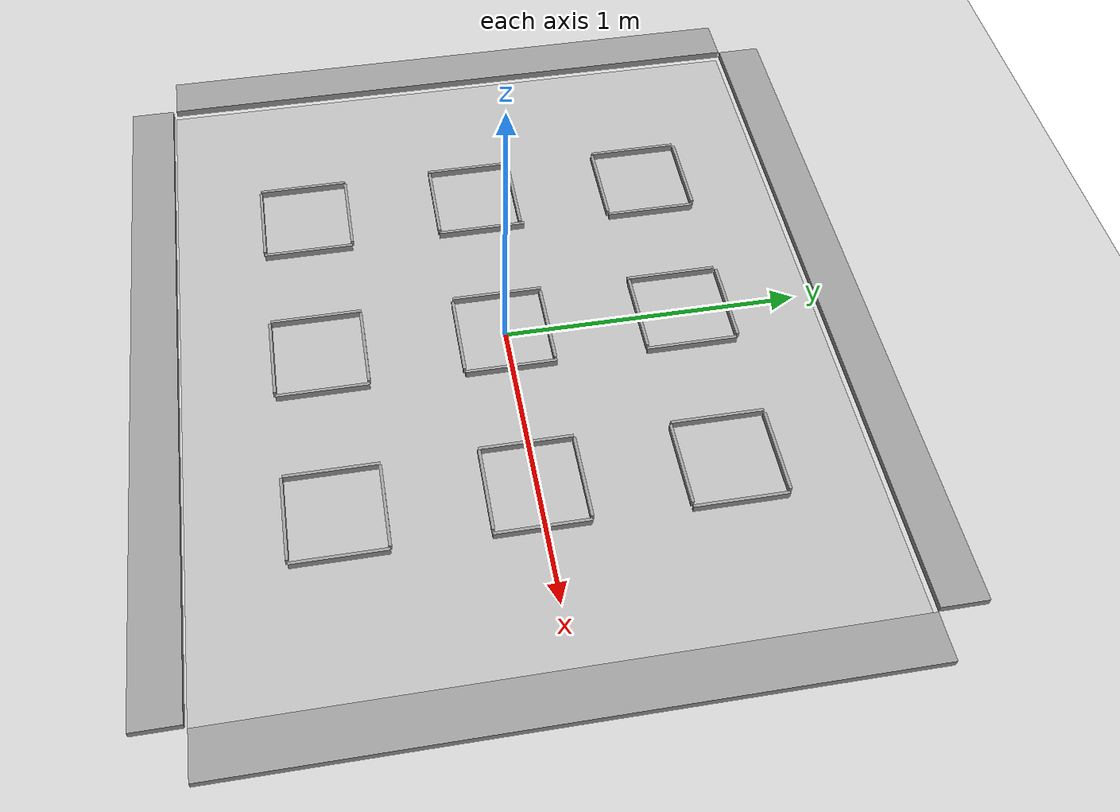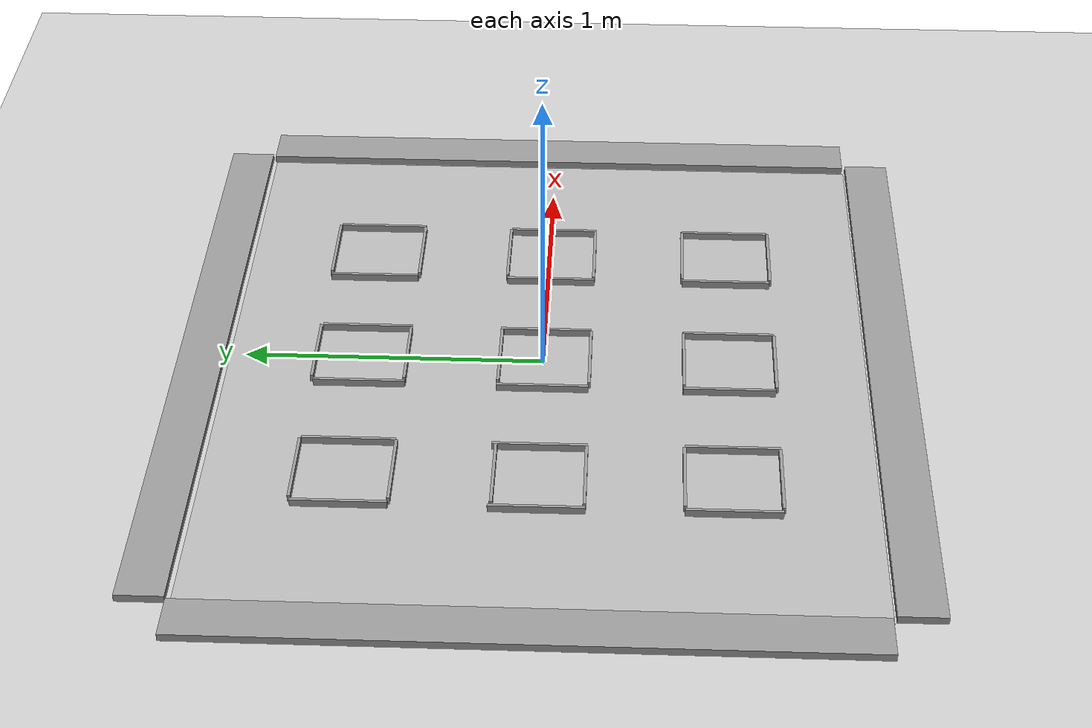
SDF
<sdf version="1.6">
 <world name="final_ps2">
  <light name="sun" type="directional">
   <pose>0 0 10 0 -0 0</pose>
   <diffuse>0.8 0.8 0.8 1</diffuse>
   <specular>0.2 0.2 0.2 1</specular>
   <attenuation>
    <range>1000</range>
    <constant>0.9</constant>
    <linear>0.01</linear>
    <quadratic>0.001</quadratic>
   </attenuation>
   <direction>-0.5 0.1 -0.9</direction>
   <spot><inner_angle>0</inner_angle><outer_angle>0</outer_angle><falloff>0</falloff></spot>
  </light>
  <model name="ground_plane">
   <static>1</static>
   <link name="link">
    <collision name="collision">
     <geometry><plane><normal>0 0 1</normal><size>100 100</size></plane></geometry>
     <surface>
      <contact><collide_bitmask>65535</collide_bitmask></contact>
      <friction><ode><mu>100</mu><mu2>50</mu2></ode></friction>
     </surface>
    </collision>
    <visual name="visual">
     <cast_shadows>0</cast_shadows>
     <geometry><plane><normal>0 0 1</normal><size>100 100</size></plane></geometry>
     <material>
      <script><uri>file://media/materials/scripts/gazebo.material</uri><name>Gazebo/Grey</name></script>
     </material>
    </visual>
   </link>
  </model>
  <gravity>0 0 -9.8</gravity>
  <magnetic_field>6e-06 2.3e-05 -4.2e-05</magnetic_field>
  <atmosphere type="adiabatic"/>
  <physics type="ode">
   <max_step_size>0.001</max_step_size>
   <real_time_factor>1</real_time_factor>
   <real_time_update_rate>1000</real_time_update_rate>
  </physics>
  <scene><ambient>0.4 0.4 0.4 1</ambient><background>0.7 0.7 0.7 1</background><shadows>1</shadows></scene>
  <spherical_coordinates>
   <surface_model>EARTH_WGS84</surface_model>
   <latitude_deg>0</latitude_deg>
   <longitude_deg>0</longitude_deg>
   <elevation>0</elevation>
   <heading_deg>0</heading_deg>
  </spherical_coordinates>
  <model name="final_ps2">
   <link name="link_0">
    <inertial>
     <mass>1</mass>
     <inertia>
      <ixx>0.166667</ixx>
      <ixy>0</ixy>
      <ixz>0</ixz>
      <iyy>0.166667</iyy>
      <iyz>0</iyz>
      <izz>0.166667</izz>
     </inertia>
    </inertial>
    <pose>1.29325 0.001795 -0.003208 0 -0 0</pose>
    <visual name="visual">
     <geometry><box><size>0.1524 2.1336 0.0254</size></box></geometry>
     <material>
      <lighting>1</lighting>
      <script><uri>file://media/materials/scripts/gazebo.material</uri><name>Gazebo/Grey</name></script>
      <shader type="pixel"><normal_map>__default__</normal_map></shader>
      <ambient>0.3 0.3 0.3 1</ambient>
      <diffuse>0.7 0.7 0.7 1</diffuse>
      <specular>0.01 0.01 0.01 1</specular>
      <emissive>0 0 0 1</emissive>
     </material>
    </visual>
    <collision name="collision">
     <geometry><box><size>1 1 1</size></box></geometry>
     <surface>
      <friction>
       <ode><mu>1</mu><mu2>1</mu2><fdir1>0 0 0</fdir1><slip1>0</slip1><slip2>0</slip2></ode>
       <torsional>
        <coefficient>1</coefficient>
        <patch_radius>0</patch_radius>
        <surface_radius>0</surface_radius>
        <use_patch_radius>1</use_patch_radius>
        <ode><slip>0</slip></ode>
       </torsional>
      </friction>
      <bounce><restitution_coefficient>0</restitution_coefficient><threshold>1e+06</threshold></bounce>
      <contact>
       <collide_without_contact>0</collide_without_contact>
       <collide_without_contact_bitmask>1</collide_without_contact_bitmask>
       <collide_bitmask>1</collide_bitmask>
       <ode>
        <soft_cfm>0</soft_cfm>
        <soft_erp>0.2</soft_erp>
        <kp>1e+13</kp>
        <kd>1</kd>
        <max_vel>0.01</max_vel>
        <min_depth>0</min_depth>
       </ode>
       <bullet>
        <split_impulse>1</split_impulse>
        <split_impulse_penetration_threshold>-0.01</split_impulse_penetration_threshold>
        <soft_cfm>0</soft_cfm>
        <soft_erp>0.2</soft_erp>
        <kp>1e+13</kp>
        <kd>1</kd>
       </bullet>
      </contact>
     </surface>
    </collision>
   </link>
   <link name="link_0_clone">
    <inertial>
     <mass>1</mass>
     <inertia>
      <ixx>0.166667</ixx>
      <ixy>0</ixy>
      <ixz>0</ixz>
      <iyy>0.166667</iyy>
      <iyz>0</iyz>
      <izz>0.166667</izz>
     </inertia>
    </inertial>
    <pose>-1.30861 0.003915 0.00674 0 -0 0</pose>
    <visual name="visual">
     <geometry><box><size>0.1524 2.1336 0.0254</size></box></geometry>
     <material>
      <lighting>1</lighting>
      <script><uri>file://media/materials/scripts/gazebo.material</uri><name>Gazebo/Grey</name></script>
      <shader type="pixel"><normal_map>__default__</normal_map></shader>
      <ambient>0.3 0.3 0.3 1</ambient>
      <diffuse>0.7 0.7 0.7 1</diffuse>
      <specular>0.01 0.01 0.01 1</specular>
      <emissive>0 0 0 1</emissive>
     </material>
    </visual>
    <collision name="collision">
     <geometry><box><size>1 1 1</size></box></geometry>
     <surface>
      <friction>
       <ode><mu>1</mu><mu2>1</mu2><fdir1>0 0 0</fdir1><slip1>0</slip1><slip2>0</slip2></ode>
       <torsional>
        <coefficient>1</coefficient>
        <patch_radius>0</patch_radius>
        <surface_radius>0</surface_radius>
        <use_patch_radius>1</use_patch_radius>
        <ode><slip>0</slip></ode>
       </torsional>
      </friction>
      <bounce><restitution_coefficient>0</restitution_coefficient><threshold>1e+06</threshold></bounce>
      <contact>
       <collide_without_contact>0</collide_without_contact>
       <collide_without_contact_bitmask>1</collide_without_contact_bitmask>
       <collide_bitmask>1</collide_bitmask>
       <ode>
        <soft_cfm>0</soft_cfm>
        <soft_erp>0.2</soft_erp>
        <kp>1e+13</kp>
        <kd>1</kd>
        <max_vel>0.01</max_vel>
        <min_depth>0</min_depth>
       </ode>
       <bullet>
        <split_impulse>1</split_impulse>
        <split_impulse_penetration_threshold>-0.01</split_impulse_penetration_threshold>
        <soft_cfm>0</soft_cfm>
        <soft_erp>0.2</soft_erp>
        <kp>1e+13</kp>
        <kd>1</kd>
       </bullet>
      </contact>
     </surface>
    </collision>
   </link>
   <link name="link_1">
    <inertial>
     <mass>1</mass>
     <inertia>
      <ixx>0.166667</ixx>
      <ixy>0</ixy>
      <ixz>0</ixz>
      <iyy>0.166667</iyy>
      <iyz>0</iyz>
      <izz>0.166667</izz>
     </inertia>
     <pose>0 1.28676 0.0128 0 -0 0</pose>
    </inertial>
    <pose>-0.009536 -1.1508 0.009064 0 -0 0</pose>
    <visual name="visual">
     <geometry><box><size>2.4384 0.1524 0.0254</size></box></geometry>
     <material>
      <lighting>1</lighting>
      <script><uri>file://media/materials/scripts/gazebo.material</uri><name>Gazebo/Grey</name></script>
      <shader type="pixel"><normal_map>__default__</normal_map></shader>
      <ambient>0.3 0.3 0.3 1</ambient>
      <diffuse>0.7 0.7 0.7 1</diffuse>
      <specular>0.01 0.01 0.01 1</specular>
      <emissive>0 0 0 1</emissive>
     </material>
    </visual>
    <collision name="collision">
     <geometry><box><size>1 1 1</size></box></geometry>
     <surface>
      <friction>
       <ode><mu>1</mu><mu2>1</mu2><fdir1>0 0 0</fdir1><slip1>0</slip1><slip2>0</slip2></ode>
       <torsional>
        <coefficient>1</coefficient>
        <patch_radius>0</patch_radius>
        <surface_radius>0</surface_radius>
        <use_patch_radius>1</use_patch_radius>
        <ode><slip>0</slip></ode>
       </torsional>
      </friction>
      <bounce><restitution_coefficient>0</restitution_coefficient><threshold>1e+06</threshold></bounce>
      <contact>
       <collide_without_contact>0</collide_without_contact>
       <collide_without_contact_bitmask>1</collide_without_contact_bitmask>
       <collide_bitmask>1</collide_bitmask>
       <ode>
        <soft_cfm>0</soft_cfm>
        <soft_erp>0.2</soft_erp>
        <kp>1e+13</kp>
        <kd>1</kd>
        <max_vel>0.01</max_vel>
        <min_depth>0</min_depth>
       </ode>
       <bullet>
        <split_impulse>1</split_impulse>
        <split_impulse_penetration_threshold>-0.01</split_impulse_penetration_threshold>
        <soft_cfm>0</soft_cfm>
        <soft_erp>0.2</soft_erp>
        <kp>1e+13</kp>
        <kd>1</kd>
       </bullet>
      </contact>
     </surface>
    </collision>
   </link>
   <link name="link_1_clone">
    <inertial>
     <mass>1</mass>
     <inertia>
      <ixx>0.166667</ixx>
      <ixy>0</ixy>
      <ixz>0</ixz>
      <iyy>0.166667</iyy>
      <iyz>0</iyz>
      <izz>0.166667</izz>
     </inertia>
     <pose>0 1.28676 0.0128 0 -0 0</pose>
    </inertial>
    <pose>-0.008231 1.15032 0.009064 0 -0 0</pose>
    <visual name="visual">
     <geometry><box><size>2.4384 0.1524 0.0254</size></box></geometry>
     <material>
      <lighting>1</lighting>
      <script><uri>file://media/materials/scripts/gazebo.material</uri><name>Gazebo/Grey</name></script>
      <shader type="pixel"><normal_map>__default__</normal_map></shader>
      <ambient>0.3 0.3 0.3 1</ambient>
      <diffuse>0.7 0.7 0.7 1</diffuse>
      <specular>0.01 0.01 0.01 1</specular>
      <emissive>0 0 0 1</emissive>
     </material>
    </visual>
    <collision name="collision">
     <geometry><box><size>1 1 1</size></box></geometry>
     <surface>
      <friction>
       <ode><mu>1</mu><mu2>1</mu2><fdir1>0 0 0</fdir1><slip1>0</slip1><slip2>0</slip2></ode>
       <torsional>
        <coefficient>1</coefficient>
        <patch_radius>0</patch_radius>
        <surface_radius>0</surface_radius>
        <use_patch_radius>1</use_patch_radius>
        <ode><slip>0</slip></ode>
       </torsional>
      </friction>
      <bounce><restitution_coefficient>0</restitution_coefficient><threshold>1e+06</threshold></bounce>
      <contact>
       <collide_without_contact>0</collide_without_contact>
       <collide_without_contact_bitmask>1</collide_without_contact_bitmask>
       <collide_bitmask>1</collide_bitmask>
       <ode>
        <soft_cfm>0</soft_cfm>
        <soft_erp>0.2</soft_erp>
        <kp>1e+13</kp>
        <kd>1</kd>
        <max_vel>0.01</max_vel>
        <min_depth>0</min_depth>
       </ode>
       <bullet>
        <split_impulse>1</split_impulse>
        <split_impulse_penetration_threshold>-0.01</split_impulse_penetration_threshold>
        <soft_cfm>0</soft_cfm>
        <soft_erp>0.2</soft_erp>
        <kp>1e+13</kp>
        <kd>1</kd>
       </bullet>
      </contact>
     </surface>
    </collision>
   </link>
   <link name="link_4">
    <inertial>
     <mass>1</mass>
     <inertia>
      <ixx>0.166667</ixx>
      <ixy>0</ixy>
      <ixz>0</ixz>
      <iyy>0.166667</iyy>
      <iyz>0</iyz>
      <izz>0.166667</izz>
     </inertia>
    </inertial>
    <pose>0.610343 -0.767629 0.001581 0 -0 0</pose>
    <visual name="visual">
     <geometry><box><size>0.2848 0.01 0.0254</size></box></geometry>
     <material>
      <lighting>1</lighting>
      <script><uri>file://media/materials/scripts/gazebo.material</uri><name>Gazebo/Grey</name></script>
      <shader type="pixel"><normal_map>__default__</normal_map></shader>
      <ambient>0.3 0.3 0.3 1</ambient>
      <diffuse>0.7 0.7 0.7 1</diffuse>
      <specular>0.01 0.01 0.01 1</specular>
      <emissive>0 0 0 1</emissive>
     </material>
    </visual>
    <collision name="collision">
     <geometry><box><size>1 1 1</size></box></geometry>
     <surface>
      <friction>
       <ode><mu>1</mu><mu2>1</mu2><fdir1>0 0 0</fdir1><slip1>0</slip1><slip2>0</slip2></ode>
       <torsional>
        <coefficient>1</coefficient>
        <patch_radius>0</patch_radius>
        <surface_radius>0</surface_radius>
        <use_patch_radius>1</use_patch_radius>
        <ode><slip>0</slip></ode>
       </torsional>
      </friction>
      <bounce><restitution_coefficient>0</restitution_coefficient><threshold>1e+06</threshold></bounce>
      <contact>
       <collide_without_contact>0</collide_without_contact>
       <collide_without_contact_bitmask>1</collide_without_contact_bitmask>
       <collide_bitmask>1</collide_bitmask>
       <ode>
        <soft_cfm>0</soft_cfm>
        <soft_erp>0.2</soft_erp>
        <kp>1e+13</kp>
        <kd>1</kd>
        <max_vel>0.01</max_vel>
        <min_depth>0</min_depth>
       </ode>
       <bullet>
        <split_impulse>1</split_impulse>
        <split_impulse_penetration_threshold>-0.01</split_impulse_penetration_threshold>
        <soft_cfm>0</soft_cfm>
        <soft_erp>0.2</soft_erp>
        <kp>1e+13</kp>
        <kd>1</kd>
       </bullet>
      </contact>
     </surface>
    </collision>
   </link>
   <link name="link_4_clone">
    <inertial>
     <mass>1</mass>
     <inertia>
      <ixx>0.166667</ixx>
      <ixy>0</ixy>
      <ixz>0</ixz>
      <iyy>0.166667</iyy>
      <iyz>0</iyz>
      <izz>0.166667</izz>
     </inertia>
    </inertial>
    <pose>0.611896 -0.461434 0.001581 0 -0 0</pose>
    <visual name="visual">
     <geometry><box><size>0.2848 0.01 0.0254</size></box></geometry>
     <material>
      <lighting>1</lighting>
      <script><uri>file://media/materials/scripts/gazebo.material</uri><name>Gazebo/Grey</name></script>
      <shader type="pixel"><normal_map>__default__</normal_map></shader>
      <ambient>0.3 0.3 0.3 1</ambient>
      <diffuse>0.7 0.7 0.7 1</diffuse>
      <specular>0.01 0.01 0.01 1</specular>
      <emissive>0 0 0 1</emissive>
     </material>
    </visual>
    <collision name="collision">
     <geometry><box><size>1 1 1</size></box></geometry>
     <surface>
      <friction>
       <ode><mu>1</mu><mu2>1</mu2><fdir1>0 0 0</fdir1><slip1>0</slip1><slip2>0</slip2></ode>
       <torsional>
        <coefficient>1</coefficient>
        <patch_radius>0</patch_radius>
        <surface_radius>0</surface_radius>
        <use_patch_radius>1</use_patch_radius>
        <ode><slip>0</slip></ode>
       </torsional>
      </friction>
      <bounce><restitution_coefficient>0</restitution_coefficient><threshold>1e+06</threshold></bounce>
      <contact>
       <collide_without_contact>0</collide_without_contact>
       <collide_without_contact_bitmask>1</collide_without_contact_bitmask>
       <collide_bitmask>1</collide_bitmask>
       <ode>
        <soft_cfm>0</soft_cfm>
        <soft_erp>0.2</soft_erp>
        <kp>1e+13</kp>
        <kd>1</kd>
        <max_vel>0.01</max_vel>
        <min_depth>0</min_depth>
       </ode>
       <bullet>
        <split_impulse>1</split_impulse>
        <split_impulse_penetration_threshold>-0.01</split_impulse_penetration_threshold>
        <soft_cfm>0</soft_cfm>
        <soft_erp>0.2</soft_erp>
        <kp>1e+13</kp>
        <kd>1</kd>
       </bullet>
      </contact>
     </surface>
    </collision>
   </link>
   <link name="link_4_clone_0">
    <inertial>
     <mass>1</mass>
     <inertia>
      <ixx>0.166667</ixx>
      <ixy>0</ixy>
      <ixz>0</ixz>
      <iyy>0.166667</iyy>
      <iyz>0</iyz>
      <izz>0.166667</izz>
     </inertia>
    </inertial>
    <pose>0.608649 0.151484 0.001581 0 -0 0</pose>
    <visual name="visual">
     <geometry><box><size>0.2848 0.01 0.0254</size></box></geometry>
     <material>
      <lighting>1</lighting>
      <script><uri>file://media/materials/scripts/gazebo.material</uri><name>Gazebo/Grey</name></script>
      <shader type="pixel"><normal_map>__default__</normal_map></shader>
      <ambient>0.3 0.3 0.3 1</ambient>
      <diffuse>0.7 0.7 0.7 1</diffuse>
      <specular>0.01 0.01 0.01 1</specular>
      <emissive>0 0 0 1</emissive>
     </material>
    </visual>
    <collision name="collision">
     <geometry><box><size>1 1 1</size></box></geometry>
     <surface>
      <friction>
       <ode><mu>1</mu><mu2>1</mu2><fdir1>0 0 0</fdir1><slip1>0</slip1><slip2>0</slip2></ode>
       <torsional>
        <coefficient>1</coefficient>
        <patch_radius>0</patch_radius>
        <surface_radius>0</surface_radius>
        <use_patch_radius>1</use_patch_radius>
        <ode><slip>0</slip></ode>
       </torsional>
      </friction>
      <bounce><restitution_coefficient>0</restitution_coefficient><threshold>1e+06</threshold></bounce>
      <contact>
       <collide_without_contact>0</collide_without_contact>
       <collide_without_contact_bitmask>1</collide_without_contact_bitmask>
       <collide_bitmask>1</collide_bitmask>
       <ode>
        <soft_cfm>0</soft_cfm>
        <soft_erp>0.2</soft_erp>
        <kp>1e+13</kp>
        <kd>1</kd>
        <max_vel>0.01</max_vel>
        <min_depth>0</min_depth>
       </ode>
       <bullet>
        <split_impulse>1</split_impulse>
        <split_impulse_penetration_threshold>-0.01</split_impulse_penetration_threshold>
        <soft_cfm>0</soft_cfm>
        <soft_erp>0.2</soft_erp>
        <kp>1e+13</kp>
        <kd>1</kd>
       </bullet>
      </contact>
     </surface>
    </collision>
   </link>
   <link name="link_4_clone_1">
    <inertial>
     <mass>1</mass>
     <inertia>
      <ixx>0.166667</ixx>
      <ixy>0</ixy>
      <ixz>0</ixz>
      <iyy>0.166667</iyy>
      <iyz>0</iyz>
      <izz>0.166667</izz>
     </inertia>
    </inertial>
    <pose>0.605772 -0.150736 0.001581 0 -0 0</pose>
    <visual name="visual">
     <geometry><box><size>0.2848 0.01 0.0254</size></box></geometry>
     <material>
      <lighting>1</lighting>
      <script><uri>file://media/materials/scripts/gazebo.material</uri><name>Gazebo/Grey</name></script>
      <shader type="pixel"><normal_map>__default__</normal_map></shader>
      <ambient>0.3 0.3 0.3 1</ambient>
      <diffuse>0.7 0.7 0.7 1</diffuse>
      <specular>0.01 0.01 0.01 1</specular>
      <emissive>0 0 0 1</emissive>
     </material>
    </visual>
    <collision name="collision">
     <geometry><box><size>1 1 1</size></box></geometry>
     <surface>
      <friction>
       <ode><mu>1</mu><mu2>1</mu2><fdir1>0 0 0</fdir1><slip1>0</slip1><slip2>0</slip2></ode>
       <torsional>
        <coefficient>1</coefficient>
        <patch_radius>0</patch_radius>
        <surface_radius>0</surface_radius>
        <use_patch_radius>1</use_patch_radius>
        <ode><slip>0</slip></ode>
       </torsional>
      </friction>
      <bounce><restitution_coefficient>0</restitution_coefficient><threshold>1e+06</threshold></bounce>
      <contact>
       <collide_without_contact>0</collide_without_contact>
       <collide_without_contact_bitmask>1</collide_without_contact_bitmask>
       <collide_bitmask>1</collide_bitmask>
       <ode>
        <soft_cfm>0</soft_cfm>
        <soft_erp>0.2</soft_erp>
        <kp>1e+13</kp>
        <kd>1</kd>
        <max_vel>0.01</max_vel>
        <min_depth>0</min_depth>
       </ode>
       <bullet>
        <split_impulse>1</split_impulse>
        <split_impulse_penetration_threshold>-0.01</split_impulse_penetration_threshold>
        <soft_cfm>0</soft_cfm>
        <soft_erp>0.2</soft_erp>
        <kp>1e+13</kp>
        <kd>1</kd>
       </bullet>
      </contact>
     </surface>
    </collision>
   </link>
   <link name="link_4_clone_10">
    <inertial>
     <mass>1</mass>
     <inertia>
      <ixx>0.166667</ixx>
      <ixy>0</ixy>
      <ixz>0</ixz>
      <iyy>0.166667</iyy>
      <iyz>0</iyz>
      <izz>0.166667</izz>
     </inertia>
    </inertial>
    <pose>-0.606723 -0.766782 0.001581 0 -0 0</pose>
    <visual name="visual">
     <geometry><box><size>0.2848 0.01 0.0254</size></box></geometry>
     <material>
      <lighting>1</lighting>
      <script><uri>file://media/materials/scripts/gazebo.material</uri><name>Gazebo/Grey</name></script>
      <shader type="pixel"><normal_map>__default__</normal_map></shader>
      <ambient>0.3 0.3 0.3 1</ambient>
      <diffuse>0.7 0.7 0.7 1</diffuse>
      <specular>0.01 0.01 0.01 1</specular>
      <emissive>0 0 0 1</emissive>
     </material>
    </visual>
    <collision name="collision">
     <geometry><box><size>1 1 1</size></box></geometry>
     <surface>
      <friction>
       <ode><mu>1</mu><mu2>1</mu2><fdir1>0 0 0</fdir1><slip1>0</slip1><slip2>0</slip2></ode>
       <torsional>
        <coefficient>1</coefficient>
        <patch_radius>0</patch_radius>
        <surface_radius>0</surface_radius>
        <use_patch_radius>1</use_patch_radius>
        <ode><slip>0</slip></ode>
       </torsional>
      </friction>
      <bounce><restitution_coefficient>0</restitution_coefficient><threshold>1e+06</threshold></bounce>
      <contact>
       <collide_without_contact>0</collide_without_contact>
       <collide_without_contact_bitmask>1</collide_without_contact_bitmask>
       <collide_bitmask>1</collide_bitmask>
       <ode>
        <soft_cfm>0</soft_cfm>
        <soft_erp>0.2</soft_erp>
        <kp>1e+13</kp>
        <kd>1</kd>
        <max_vel>0.01</max_vel>
        <min_depth>0</min_depth>
       </ode>
       <bullet>
        <split_impulse>1</split_impulse>
        <split_impulse_penetration_threshold>-0.01</split_impulse_penetration_threshold>
        <soft_cfm>0</soft_cfm>
        <soft_erp>0.2</soft_erp>
        <kp>1e+13</kp>
        <kd>1</kd>
       </bullet>
      </contact>
     </surface>
    </collision>
   </link>
   <link name="link_4_clone_11">
    <inertial>
     <mass>1</mass>
     <inertia>
      <ixx>0.166667</ixx>
      <ixy>0</ixy>
      <ixz>0</ixz>
      <iyy>0.166667</iyy>
      <iyz>0</iyz>
      <izz>0.166667</izz>
     </inertia>
    </inertial>
    <pose>-0.608421 -0.461422 0.001581 0 -0 0</pose>
    <visual name="visual">
     <geometry><box><size>0.2848 0.01 0.0254</size></box></geometry>
     <material>
      <lighting>1</lighting>
      <script><uri>file://media/materials/scripts/gazebo.material</uri><name>Gazebo/Grey</name></script>
      <shader type="pixel"><normal_map>__default__</normal_map></shader>
      <ambient>0.3 0.3 0.3 1</ambient>
      <diffuse>0.7 0.7 0.7 1</diffuse>
      <specular>0.01 0.01 0.01 1</specular>
      <emissive>0 0 0 1</emissive>
     </material>
    </visual>
    <collision name="collision">
     <geometry><box><size>1 1 1</size></box></geometry>
     <surface>
      <friction>
       <ode><mu>1</mu><mu2>1</mu2><fdir1>0 0 0</fdir1><slip1>0</slip1><slip2>0</slip2></ode>
       <torsional>
        <coefficient>1</coefficient>
        <patch_radius>0</patch_radius>
        <surface_radius>0</surface_radius>
        <use_patch_radius>1</use_patch_radius>
        <ode><slip>0</slip></ode>
       </torsional>
      </friction>
      <bounce><restitution_coefficient>0</restitution_coefficient><threshold>1e+06</threshold></bounce>
      <contact>
       <collide_without_contact>0</collide_without_contact>
       <collide_without_contact_bitmask>1</collide_without_contact_bitmask>
       <collide_bitmask>1</collide_bitmask>
       <ode>
        <soft_cfm>0</soft_cfm>
        <soft_erp>0.2</soft_erp>
        <kp>1e+13</kp>
        <kd>1</kd>
        <max_vel>0.01</max_vel>
        <min_depth>0</min_depth>
       </ode>
       <bullet>
        <split_impulse>1</split_impulse>
        <split_impulse_penetration_threshold>-0.01</split_impulse_penetration_threshold>
        <soft_cfm>0</soft_cfm>
        <soft_erp>0.2</soft_erp>
        <kp>1e+13</kp>
        <kd>1</kd>
       </bullet>
      </contact>
     </surface>
    </collision>
   </link>
   <link name="link_4_clone_12">
    <inertial>
     <mass>1</mass>
     <inertia>
      <ixx>0.166667</ixx>
      <ixy>0</ixy>
      <ixz>0</ixz>
      <iyy>0.166667</iyy>
      <iyz>0</iyz>
      <izz>0.166667</izz>
     </inertia>
    </inertial>
    <pose>-0.611651 -0.149933 0.001581 0 -0 0</pose>
    <visual name="visual">
     <geometry><box><size>0.2848 0.01 0.0254</size></box></geometry>
     <material>
      <lighting>1</lighting>
      <script><uri>file://media/materials/scripts/gazebo.material</uri><name>Gazebo/Grey</name></script>
      <shader type="pixel"><normal_map>__default__</normal_map></shader>
      <ambient>0.3 0.3 0.3 1</ambient>
      <diffuse>0.7 0.7 0.7 1</diffuse>
      <specular>0.01 0.01 0.01 1</specular>
      <emissive>0 0 0 1</emissive>
     </material>
    </visual>
    <collision name="collision">
     <geometry><box><size>1 1 1</size></box></geometry>
     <surface>
      <friction>
       <ode><mu>1</mu><mu2>1</mu2><fdir1>0 0 0</fdir1><slip1>0</slip1><slip2>0</slip2></ode>
       <torsional>
        <coefficient>1</coefficient>
        <patch_radius>0</patch_radius>
        <surface_radius>0</surface_radius>
        <use_patch_radius>1</use_patch_radius>
        <ode><slip>0</slip></ode>
       </torsional>
      </friction>
      <bounce><restitution_coefficient>0</restitution_coefficient><threshold>1e+06</threshold></bounce>
      <contact>
       <collide_without_contact>0</collide_without_contact>
       <collide_without_contact_bitmask>1</collide_without_contact_bitmask>
       <collide_bitmask>1</collide_bitmask>
       <ode>
        <soft_cfm>0</soft_cfm>
        <soft_erp>0.2</soft_erp>
        <kp>1e+13</kp>
        <kd>1</kd>
        <max_vel>0.01</max_vel>
        <min_depth>0</min_depth>
       </ode>
       <bullet>
        <split_impulse>1</split_impulse>
        <split_impulse_penetration_threshold>-0.01</split_impulse_penetration_threshold>
        <soft_cfm>0</soft_cfm>
        <soft_erp>0.2</soft_erp>
        <kp>1e+13</kp>
        <kd>1</kd>
       </bullet>
      </contact>
     </surface>
    </collision>
   </link>
   <link name="link_4_clone_13">
    <inertial>
     <mass>1</mass>
     <inertia>
      <ixx>0.166667</ixx>
      <ixy>0</ixy>
      <ixz>0</ixz>
      <iyy>0.166667</iyy>
      <iyz>0</iyz>
      <izz>0.166667</izz>
     </inertia>
    </inertial>
    <pose>-0.611369 0.139855 0.001581 0 -0 0</pose>
    <visual name="visual">
     <geometry><box><size>0.2848 0.01 0.0254</size></box></geometry>
     <material>
      <lighting>1</lighting>
      <script><uri>file://media/materials/scripts/gazebo.material</uri><name>Gazebo/Grey</name></script>
      <shader type="pixel"><normal_map>__default__</normal_map></shader>
      <ambient>0.3 0.3 0.3 1</ambient>
      <diffuse>0.7 0.7 0.7 1</diffuse>
      <specular>0.01 0.01 0.01 1</specular>
      <emissive>0 0 0 1</emissive>
     </material>
    </visual>
    <collision name="collision">
     <geometry><box><size>1 1 1</size></box></geometry>
     <surface>
      <friction>
       <ode><mu>1</mu><mu2>1</mu2><fdir1>0 0 0</fdir1><slip1>0</slip1><slip2>0</slip2></ode>
       <torsional>
        <coefficient>1</coefficient>
        <patch_radius>0</patch_radius>
        <surface_radius>0</surface_radius>
        <use_patch_radius>1</use_patch_radius>
        <ode><slip>0</slip></ode>
       </torsional>
      </friction>
      <bounce><restitution_coefficient>0</restitution_coefficient><threshold>1e+06</threshold></bounce>
      <contact>
       <collide_without_contact>0</collide_without_contact>
       <collide_without_contact_bitmask>1</collide_without_contact_bitmask>
       <collide_bitmask>1</collide_bitmask>
       <ode>
        <soft_cfm>0</soft_cfm>
        <soft_erp>0.2</soft_erp>
        <kp>1e+13</kp>
        <kd>1</kd>
        <max_vel>0.01</max_vel>
        <min_depth>0</min_depth>
       </ode>
       <bullet>
        <split_impulse>1</split_impulse>
        <split_impulse_penetration_threshold>-0.01</split_impulse_penetration_threshold>
        <soft_cfm>0</soft_cfm>
        <soft_erp>0.2</soft_erp>
        <kp>1e+13</kp>
        <kd>1</kd>
       </bullet>
      </contact>
     </surface>
    </collision>
   </link>
   <link name="link_4_clone_14">
    <inertial>
     <mass>1</mass>
     <inertia>
      <ixx>0.166667</ixx>
      <ixy>0</ixy>
      <ixz>0</ixz>
      <iyy>0.166667</iyy>
      <iyz>0</iyz>
      <izz>0.166667</izz>
     </inertia>
    </inertial>
    <pose>-0.607319 0.458844 0.001581 0 -0 0</pose>
    <visual name="visual">
     <geometry><box><size>0.2848 0.01 0.0254</size></box></geometry>
     <material>
      <lighting>1</lighting>
      <script><uri>file://media/materials/scripts/gazebo.material</uri><name>Gazebo/Grey</name></script>
      <shader type="pixel"><normal_map>__default__</normal_map></shader>
      <ambient>0.3 0.3 0.3 1</ambient>
      <diffuse>0.7 0.7 0.7 1</diffuse>
      <specular>0.01 0.01 0.01 1</specular>
      <emissive>0 0 0 1</emissive>
     </material>
    </visual>
    <collision name="collision">
     <geometry><box><size>1 1 1</size></box></geometry>
     <surface>
      <friction>
       <ode><mu>1</mu><mu2>1</mu2><fdir1>0 0 0</fdir1><slip1>0</slip1><slip2>0</slip2></ode>
       <torsional>
        <coefficient>1</coefficient>
        <patch_radius>0</patch_radius>
        <surface_radius>0</surface_radius>
        <use_patch_radius>1</use_patch_radius>
        <ode><slip>0</slip></ode>
       </torsional>
      </friction>
      <bounce><restitution_coefficient>0</restitution_coefficient><threshold>1e+06</threshold></bounce>
      <contact>
       <collide_without_contact>0</collide_without_contact>
       <collide_without_contact_bitmask>1</collide_without_contact_bitmask>
       <collide_bitmask>1</collide_bitmask>
       <ode>
        <soft_cfm>0</soft_cfm>
        <soft_erp>0.2</soft_erp>
        <kp>1e+13</kp>
        <kd>1</kd>
        <max_vel>0.01</max_vel>
        <min_depth>0</min_depth>
       </ode>
       <bullet>
        <split_impulse>1</split_impulse>
        <split_impulse_penetration_threshold>-0.01</split_impulse_penetration_threshold>
        <soft_cfm>0</soft_cfm>
        <soft_erp>0.2</soft_erp>
        <kp>1e+13</kp>
        <kd>1</kd>
       </bullet>
      </contact>
     </surface>
    </collision>
   </link>
   <link name="link_4_clone_15">
    <inertial>
     <mass>1</mass>
     <inertia>
      <ixx>0.166667</ixx>
      <ixy>0</ixy>
      <ixz>0</ixz>
      <iyy>0.166667</iyy>
      <iyz>0</iyz>
      <izz>0.166667</izz>
     </inertia>
    </inertial>
    <pose>-0.606551 0.768687 0.001581 0 -0 0</pose>
    <visual name="visual">
     <geometry><box><size>0.2848 0.01 0.0254</size></box></geometry>
     <material>
      <lighting>1</lighting>
      <script><uri>file://media/materials/scripts/gazebo.material</uri><name>Gazebo/Grey</name></script>
      <shader type="pixel"><normal_map>__default__</normal_map></shader>
      <ambient>0.3 0.3 0.3 1</ambient>
      <diffuse>0.7 0.7 0.7 1</diffuse>
      <specular>0.01 0.01 0.01 1</specular>
      <emissive>0 0 0 1</emissive>
     </material>
    </visual>
    <collision name="collision">
     <geometry><box><size>1 1 1</size></box></geometry>
     <surface>
      <friction>
       <ode><mu>1</mu><mu2>1</mu2><fdir1>0 0 0</fdir1><slip1>0</slip1><slip2>0</slip2></ode>
       <torsional>
        <coefficient>1</coefficient>
        <patch_radius>0</patch_radius>
        <surface_radius>0</surface_radius>
        <use_patch_radius>1</use_patch_radius>
        <ode><slip>0</slip></ode>
       </torsional>
      </friction>
      <bounce><restitution_coefficient>0</restitution_coefficient><threshold>1e+06</threshold></bounce>
      <contact>
       <collide_without_contact>0</collide_without_contact>
       <collide_without_contact_bitmask>1</collide_without_contact_bitmask>
       <collide_bitmask>1</collide_bitmask>
       <ode>
        <soft_cfm>0</soft_cfm>
        <soft_erp>0.2</soft_erp>
        <kp>1e+13</kp>
        <kd>1</kd>
        <max_vel>0.01</max_vel>
        <min_depth>0</min_depth>
       </ode>
       <bullet>
        <split_impulse>1</split_impulse>
        <split_impulse_penetration_threshold>-0.01</split_impulse_penetration_threshold>
        <soft_cfm>0</soft_cfm>
        <soft_erp>0.2</soft_erp>
        <kp>1e+13</kp>
        <kd>1</kd>
       </bullet>
      </contact>
     </surface>
    </collision>
   </link>
   <link name="link_4_clone_2">
    <inertial>
     <mass>1</mass>
     <inertia>
      <ixx>0.166667</ixx>
      <ixy>0</ixy>
      <ixz>0</ixz>
      <iyy>0.166667</iyy>
      <iyz>0</iyz>
      <izz>0.166667</izz>
     </inertia>
    </inertial>
    <pose>0.612848 0.768954 0.001581 0 -0 0</pose>
    <visual name="visual">
     <geometry><box><size>0.2848 0.01 0.0254</size></box></geometry>
     <material>
      <lighting>1</lighting>
      <script><uri>file://media/materials/scripts/gazebo.material</uri><name>Gazebo/Grey</name></script>
      <shader type="pixel"><normal_map>__default__</normal_map></shader>
      <ambient>0.3 0.3 0.3 1</ambient>
      <diffuse>0.7 0.7 0.7 1</diffuse>
      <specular>0.01 0.01 0.01 1</specular>
      <emissive>0 0 0 1</emissive>
     </material>
    </visual>
    <collision name="collision">
     <geometry><box><size>1 1 1</size></box></geometry>
     <surface>
      <friction>
       <ode><mu>1</mu><mu2>1</mu2><fdir1>0 0 0</fdir1><slip1>0</slip1><slip2>0</slip2></ode>
       <torsional>
        <coefficient>1</coefficient>
        <patch_radius>0</patch_radius>
        <surface_radius>0</surface_radius>
        <use_patch_radius>1</use_patch_radius>
        <ode><slip>0</slip></ode>
       </torsional>
      </friction>
      <bounce><restitution_coefficient>0</restitution_coefficient><threshold>1e+06</threshold></bounce>
      <contact>
       <collide_without_contact>0</collide_without_contact>
       <collide_without_contact_bitmask>1</collide_without_contact_bitmask>
       <collide_bitmask>1</collide_bitmask>
       <ode>
        <soft_cfm>0</soft_cfm>
        <soft_erp>0.2</soft_erp>
        <kp>1e+13</kp>
        <kd>1</kd>
        <max_vel>0.01</max_vel>
        <min_depth>0</min_depth>
       </ode>
       <bullet>
        <split_impulse>1</split_impulse>
        <split_impulse_penetration_threshold>-0.01</split_impulse_penetration_threshold>
        <soft_cfm>0</soft_cfm>
        <soft_erp>0.2</soft_erp>
        <kp>1e+13</kp>
        <kd>1</kd>
       </bullet>
      </contact>
     </surface>
    </collision>
   </link>
   <link name="link_4_clone_3">
    <inertial>
     <mass>1</mass>
     <inertia>
      <ixx>0.166667</ixx>
      <ixy>0</ixy>
      <ixz>0</ixz>
      <iyy>0.166667</iyy>
      <iyz>0</iyz>
      <izz>0.166667</izz>
     </inertia>
    </inertial>
    <pose>0.611092 0.462268 0.001581 0 -0 0</pose>
    <visual name="visual">
     <geometry><box><size>0.2848 0.01 0.0254</size></box></geometry>
     <material>
      <lighting>1</lighting>
      <script><uri>file://media/materials/scripts/gazebo.material</uri><name>Gazebo/Grey</name></script>
      <shader type="pixel"><normal_map>__default__</normal_map></shader>
      <ambient>0.3 0.3 0.3 1</ambient>
      <diffuse>0.7 0.7 0.7 1</diffuse>
      <specular>0.01 0.01 0.01 1</specular>
      <emissive>0 0 0 1</emissive>
     </material>
    </visual>
    <collision name="collision">
     <geometry><box><size>1 1 1</size></box></geometry>
     <surface>
      <friction>
       <ode><mu>1</mu><mu2>1</mu2><fdir1>0 0 0</fdir1><slip1>0</slip1><slip2>0</slip2></ode>
       <torsional>
        <coefficient>1</coefficient>
        <patch_radius>0</patch_radius>
        <surface_radius>0</surface_radius>
        <use_patch_radius>1</use_patch_radius>
        <ode><slip>0</slip></ode>
       </torsional>
      </friction>
      <bounce><restitution_coefficient>0</restitution_coefficient><threshold>1e+06</threshold></bounce>
      <contact>
       <collide_without_contact>0</collide_without_contact>
       <collide_without_contact_bitmask>1</collide_without_contact_bitmask>
       <collide_bitmask>1</collide_bitmask>
       <ode>
        <soft_cfm>0</soft_cfm>
        <soft_erp>0.2</soft_erp>
        <kp>1e+13</kp>
        <kd>1</kd>
        <max_vel>0.01</max_vel>
        <min_depth>0</min_depth>
       </ode>
       <bullet>
        <split_impulse>1</split_impulse>
        <split_impulse_penetration_threshold>-0.01</split_impulse_penetration_threshold>
        <soft_cfm>0</soft_cfm>
        <soft_erp>0.2</soft_erp>
        <kp>1e+13</kp>
        <kd>1</kd>
       </bullet>
      </contact>
     </surface>
    </collision>
   </link>
   <link name="link_4_clone_4">
    <inertial>
     <mass>1</mass>
     <inertia>
      <ixx>0.166667</ixx>
      <ixy>0</ixy>
      <ixz>0</ixz>
      <iyy>0.166667</iyy>
      <iyz>0</iyz>
      <izz>0.166667</izz>
     </inertia>
    </inertial>
    <pose>0.003866 0.462986 0.001581 0 -0 0</pose>
    <visual name="visual">
     <geometry><box><size>0.2848 0.01 0.0254</size></box></geometry>
     <material>
      <lighting>1</lighting>
      <script><uri>file://media/materials/scripts/gazebo.material</uri><name>Gazebo/Grey</name></script>
      <shader type="pixel"><normal_map>__default__</normal_map></shader>
      <ambient>0.3 0.3 0.3 1</ambient>
      <diffuse>0.7 0.7 0.7 1</diffuse>
      <specular>0.01 0.01 0.01 1</specular>
      <emissive>0 0 0 1</emissive>
     </material>
    </visual>
    <collision name="collision">
     <geometry><box><size>1 1 1</size></box></geometry>
     <surface>
      <friction>
       <ode><mu>1</mu><mu2>1</mu2><fdir1>0 0 0</fdir1><slip1>0</slip1><slip2>0</slip2></ode>
       <torsional>
        <coefficient>1</coefficient>
        <patch_radius>0</patch_radius>
        <surface_radius>0</surface_radius>
        <use_patch_radius>1</use_patch_radius>
        <ode><slip>0</slip></ode>
       </torsional>
      </friction>
      <bounce><restitution_coefficient>0</restitution_coefficient><threshold>1e+06</threshold></bounce>
      <contact>
       <collide_without_contact>0</collide_without_contact>
       <collide_without_contact_bitmask>1</collide_without_contact_bitmask>
       <collide_bitmask>1</collide_bitmask>
       <ode>
        <soft_cfm>0</soft_cfm>
        <soft_erp>0.2</soft_erp>
        <kp>1e+13</kp>
        <kd>1</kd>
        <max_vel>0.01</max_vel>
        <min_depth>0</min_depth>
       </ode>
       <bullet>
        <split_impulse>1</split_impulse>
        <split_impulse_penetration_threshold>-0.01</split_impulse_penetration_threshold>
        <soft_cfm>0</soft_cfm>
        <soft_erp>0.2</soft_erp>
        <kp>1e+13</kp>
        <kd>1</kd>
       </bullet>
      </contact>
     </surface>
    </collision>
   </link>
   <link name="link_4_clone_5">
    <inertial>
     <mass>1</mass>
     <inertia>
      <ixx>0.166667</ixx>
      <ixy>0</ixy>
      <ixz>0</ixz>
      <iyy>0.166667</iyy>
      <iyz>0</iyz>
      <izz>0.166667</izz>
     </inertia>
    </inertial>
    <pose>0.006115 0.769658 0.001581 0 -0 0</pose>
    <visual name="visual">
     <geometry><box><size>0.2848 0.01 0.0254</size></box></geometry>
     <material>
      <lighting>1</lighting>
      <script><uri>file://media/materials/scripts/gazebo.material</uri><name>Gazebo/Grey</name></script>
      <shader type="pixel"><normal_map>__default__</normal_map></shader>
      <ambient>0.3 0.3 0.3 1</ambient>
      <diffuse>0.7 0.7 0.7 1</diffuse>
      <specular>0.01 0.01 0.01 1</specular>
      <emissive>0 0 0 1</emissive>
     </material>
    </visual>
    <collision name="collision">
     <geometry><box><size>1 1 1</size></box></geometry>
     <surface>
      <friction>
       <ode><mu>1</mu><mu2>1</mu2><fdir1>0 0 0</fdir1><slip1>0</slip1><slip2>0</slip2></ode>
       <torsional>
        <coefficient>1</coefficient>
        <patch_radius>0</patch_radius>
        <surface_radius>0</surface_radius>
        <use_patch_radius>1</use_patch_radius>
        <ode><slip>0</slip></ode>
       </torsional>
      </friction>
      <bounce><restitution_coefficient>0</restitution_coefficient><threshold>1e+06</threshold></bounce>
      <contact>
       <collide_without_contact>0</collide_without_contact>
       <collide_without_contact_bitmask>1</collide_without_contact_bitmask>
       <collide_bitmask>1</collide_bitmask>
       <ode>
        <soft_cfm>0</soft_cfm>
        <soft_erp>0.2</soft_erp>
        <kp>1e+13</kp>
        <kd>1</kd>
        <max_vel>0.01</max_vel>
        <min_depth>0</min_depth>
       </ode>
       <bullet>
        <split_impulse>1</split_impulse>
        <split_impulse_penetration_threshold>-0.01</split_impulse_penetration_threshold>
        <soft_cfm>0</soft_cfm>
        <soft_erp>0.2</soft_erp>
        <kp>1e+13</kp>
        <kd>1</kd>
       </bullet>
      </contact>
     </surface>
    </collision>
   </link>
   <link name="link_4_clone_6">
    <inertial>
     <mass>1</mass>
     <inertia>
      <ixx>0.166667</ixx>
      <ixy>0</ixy>
      <ixz>0</ixz>
      <iyy>0.166667</iyy>
      <iyz>0</iyz>
      <izz>0.166667</izz>
     </inertia>
    </inertial>
    <pose>0.003916 0.152123 0.001581 0 -0 0</pose>
    <visual name="visual">
     <geometry><box><size>0.2848 0.01 0.0254</size></box></geometry>
     <material>
      <lighting>1</lighting>
      <script><uri>file://media/materials/scripts/gazebo.material</uri><name>Gazebo/Grey</name></script>
      <shader type="pixel"><normal_map>__default__</normal_map></shader>
      <ambient>0.3 0.3 0.3 1</ambient>
      <diffuse>0.7 0.7 0.7 1</diffuse>
      <specular>0.01 0.01 0.01 1</specular>
      <emissive>0 0 0 1</emissive>
     </material>
    </visual>
    <collision name="collision">
     <geometry><box><size>1 1 1</size></box></geometry>
     <surface>
      <friction>
       <ode><mu>1</mu><mu2>1</mu2><fdir1>0 0 0</fdir1><slip1>0</slip1><slip2>0</slip2></ode>
       <torsional>
        <coefficient>1</coefficient>
        <patch_radius>0</patch_radius>
        <surface_radius>0</surface_radius>
        <use_patch_radius>1</use_patch_radius>
        <ode><slip>0</slip></ode>
       </torsional>
      </friction>
      <bounce><restitution_coefficient>0</restitution_coefficient><threshold>1e+06</threshold></bounce>
      <contact>
       <collide_without_contact>0</collide_without_contact>
       <collide_without_contact_bitmask>1</collide_without_contact_bitmask>
       <collide_bitmask>1</collide_bitmask>
       <ode>
        <soft_cfm>0</soft_cfm>
        <soft_erp>0.2</soft_erp>
        <kp>1e+13</kp>
        <kd>1</kd>
        <max_vel>0.01</max_vel>
        <min_depth>0</min_depth>
       </ode>
       <bullet>
        <split_impulse>1</split_impulse>
        <split_impulse_penetration_threshold>-0.01</split_impulse_penetration_threshold>
        <soft_cfm>0</soft_cfm>
        <soft_erp>0.2</soft_erp>
        <kp>1e+13</kp>
        <kd>1</kd>
       </bullet>
      </contact>
     </surface>
    </collision>
   </link>
   <link name="link_4_clone_7">
    <inertial>
     <mass>1</mass>
     <inertia>
      <ixx>0.166667</ixx>
      <ixy>0</ixy>
      <ixz>0</ixz>
      <iyy>0.166667</iyy>
      <iyz>0</iyz>
      <izz>0.166667</izz>
     </inertia>
    </inertial>
    <pose>0.00308 -0.1495 0.001581 0 -0 0</pose>
    <visual name="visual">
     <geometry><box><size>0.2848 0.01 0.0254</size></box></geometry>
     <material>
      <lighting>1</lighting>
      <script><uri>file://media/materials/scripts/gazebo.material</uri><name>Gazebo/Grey</name></script>
      <shader type="pixel"><normal_map>__default__</normal_map></shader>
      <ambient>0.3 0.3 0.3 1</ambient>
      <diffuse>0.7 0.7 0.7 1</diffuse>
      <specular>0.01 0.01 0.01 1</specular>
      <emissive>0 0 0 1</emissive>
     </material>
    </visual>
    <collision name="collision">
     <geometry><box><size>1 1 1</size></box></geometry>
     <surface>
      <friction>
       <ode><mu>1</mu><mu2>1</mu2><fdir1>0 0 0</fdir1><slip1>0</slip1><slip2>0</slip2></ode>
       <torsional>
        <coefficient>1</coefficient>
        <patch_radius>0</patch_radius>
        <surface_radius>0</surface_radius>
        <use_patch_radius>1</use_patch_radius>
        <ode><slip>0</slip></ode>
       </torsional>
      </friction>
      <bounce><restitution_coefficient>0</restitution_coefficient><threshold>1e+06</threshold></bounce>
      <contact>
       <collide_without_contact>0</collide_without_contact>
       <collide_without_contact_bitmask>1</collide_without_contact_bitmask>
       <collide_bitmask>1</collide_bitmask>
       <ode>
        <soft_cfm>0</soft_cfm>
        <soft_erp>0.2</soft_erp>
        <kp>1e+13</kp>
        <kd>1</kd>
        <max_vel>0.01</max_vel>
        <min_depth>0</min_depth>
       </ode>
       <bullet>
        <split_impulse>1</split_impulse>
        <split_impulse_penetration_threshold>-0.01</split_impulse_penetration_threshold>
        <soft_cfm>0</soft_cfm>
        <soft_erp>0.2</soft_erp>
        <kp>1e+13</kp>
        <kd>1</kd>
       </bullet>
      </contact>
     </surface>
    </collision>
   </link>
   <link name="link_4_clone_8">
    <inertial>
     <mass>1</mass>
     <inertia>
      <ixx>0.166667</ixx>
      <ixy>0</ixy>
      <ixz>0</ixz>
      <iyy>0.166667</iyy>
      <iyz>0</iyz>
      <izz>0.166667</izz>
     </inertia>
    </inertial>
    <pose>0.000293 -0.463289 0.001581 0 -0 0</pose>
    <visual name="visual">
     <geometry><box><size>0.2848 0.01 0.0254</size></box></geometry>
     <material>
      <lighting>1</lighting>
      <script><uri>file://media/materials/scripts/gazebo.material</uri><name>Gazebo/Grey</name></script>
      <shader type="pixel"><normal_map>__default__</normal_map></shader>
      <ambient>0.3 0.3 0.3 1</ambient>
      <diffuse>0.7 0.7 0.7 1</diffuse>
      <specular>0.01 0.01 0.01 1</specular>
      <emissive>0 0 0 1</emissive>
     </material>
    </visual>
    <collision name="collision">
     <geometry><box><size>1 1 1</size></box></geometry>
     <surface>
      <friction>
       <ode><mu>1</mu><mu2>1</mu2><fdir1>0 0 0</fdir1><slip1>0</slip1><slip2>0</slip2></ode>
       <torsional>
        <coefficient>1</coefficient>
        <patch_radius>0</patch_radius>
        <surface_radius>0</surface_radius>
        <use_patch_radius>1</use_patch_radius>
        <ode><slip>0</slip></ode>
       </torsional>
      </friction>
      <bounce><restitution_coefficient>0</restitution_coefficient><threshold>1e+06</threshold></bounce>
      <contact>
       <collide_without_contact>0</collide_without_contact>
       <collide_without_contact_bitmask>1</collide_without_contact_bitmask>
       <collide_bitmask>1</collide_bitmask>
       <ode>
        <soft_cfm>0</soft_cfm>
        <soft_erp>0.2</soft_erp>
        <kp>1e+13</kp>
        <kd>1</kd>
        <max_vel>0.01</max_vel>
        <min_depth>0</min_depth>
       </ode>
       <bullet>
        <split_impulse>1</split_impulse>
        <split_impulse_penetration_threshold>-0.01</split_impulse_penetration_threshold>
        <soft_cfm>0</soft_cfm>
        <soft_erp>0.2</soft_erp>
        <kp>1e+13</kp>
        <kd>1</kd>
       </bullet>
      </contact>
     </surface>
    </collision>
   </link>
   <link name="link_4_clone_9">
    <inertial>
     <mass>1</mass>
     <inertia>
      <ixx>0.166667</ixx>
      <ixy>0</ixy>
      <ixz>0</ixz>
      <iyy>0.166667</iyy>
      <iyz>0</iyz>
      <izz>0.166667</izz>
     </inertia>
    </inertial>
    <pose>-0.000704 -0.768222 0.001581 0 -0 0</pose>
    <visual name="visual">
     <geometry><box><size>0.2848 0.01 0.0254</size></box></geometry>
     <material>
      <lighting>1</lighting>
      <script><uri>file://media/materials/scripts/gazebo.material</uri><name>Gazebo/Grey</name></script>
      <shader type="pixel"><normal_map>__default__</normal_map></shader>
      <ambient>0.3 0.3 0.3 1</ambient>
      <diffuse>0.7 0.7 0.7 1</diffuse>
      <specular>0.01 0.01 0.01 1</specular>
      <emissive>0 0 0 1</emissive>
     </material>
    </visual>
    <collision name="collision">
     <geometry><box><size>1 1 1</size></box></geometry>
     <surface>
      <friction>
       <ode><mu>1</mu><mu2>1</mu2><fdir1>0 0 0</fdir1><slip1>0</slip1><slip2>0</slip2></ode>
       <torsional>
        <coefficient>1</coefficient>
        <patch_radius>0</patch_radius>
        <surface_radius>0</surface_radius>
        <use_patch_radius>1</use_patch_radius>
        <ode><slip>0</slip></ode>
       </torsional>
      </friction>
      <bounce><restitution_coefficient>0</restitution_coefficient><threshold>1e+06</threshold></bounce>
      <contact>
       <collide_without_contact>0</collide_without_contact>
       <collide_without_contact_bitmask>1</collide_without_contact_bitmask>
       <collide_bitmask>1</collide_bitmask>
       <ode>
        <soft_cfm>0</soft_cfm>
        <soft_erp>0.2</soft_erp>
        <kp>1e+13</kp>
        <kd>1</kd>
        <max_vel>0.01</max_vel>
        <min_depth>0</min_depth>
       </ode>
       <bullet>
        <split_impulse>1</split_impulse>
        <split_impulse_penetration_threshold>-0.01</split_impulse_penetration_threshold>
        <soft_cfm>0</soft_cfm>
        <soft_erp>0.2</soft_erp>
        <kp>1e+13</kp>
        <kd>1</kd>
       </bullet>
      </contact>
     </surface>
    </collision>
   </link>
   <model name="Untitled">
    <static>1</static>
    <link name="link">
     <collision name="collision">
      <geometry><plane><normal>0 0 1</normal><size>2.4384 2.1336</size></plane></geometry>
      <surface><friction><ode><mu>100</mu><mu2>50</mu2></ode></friction></surface>
     </collision>
     <visual name="visual">
      <cast_shadows>0</cast_shadows>
      <geometry><plane><normal>0 0 1</normal><size>2.4384 2.1336</size></plane></geometry>
      <material>
       <script>
        <uri>file://ps2_ground_plane/materials/scripts</uri>
        <uri>file://ps2_ground_plane/materials/textures</uri>
        <name>Ps2GroundPlane/Image</name>
       </script>
      </material>
     </visual>
    </link>
    <pose>-0.00524 -0.003554 -0.016008 0 -0 0</pose>
   </model>
   <model name="unit_box">
    <link name="link">
     <inertial>
      <mass>0.00206101</mass>
      <inertia>
       <ixx>3.735e-05</ixx>
       <ixy>0</ixy>
       <ixz>0</ixz>
       <iyy>1.638e-05</iyy>
       <iyz>0</iyz>
       <izz>2.11e-05</izz>
      </inertia>
     </inertial>
     <visual name="visual">
      <geometry><box><size>0.01 0.3048 0.0254</size></box></geometry>
      <material>
       <script><name>Gazebo/Grey</name><uri>file://media/materials/scripts/gazebo.material</uri></script>
       <shader type="pixel"><normal_map>__default__</normal_map></shader>
       <ambient>0.3 0.3 0.3 1</ambient>
       <diffuse>0.7 0.7 0.7 1</diffuse>
       <specular>0.01 0.01 0.01 1</specular>
       <emissive>0 0 0 1</emissive>
      </material>
     </visual>
     <collision name="collision">
      <geometry><box><size>0.019132 0.349942 0.308219</size></box></geometry>
      <surface>
       <friction>
        <ode><mu>1</mu><mu2>1</mu2><fdir1>0 0 0</fdir1><slip1>0</slip1><slip2>0</slip2></ode>
        <torsional>
         <coefficient>1</coefficient>
         <patch_radius>0</patch_radius>
         <surface_radius>0</surface_radius>
         <use_patch_radius>1</use_patch_radius>
         <ode><slip>0</slip></ode>
        </torsional>
       </friction>
       <bounce><restitution_coefficient>0</restitution_coefficient><threshold>1e+06</threshold></bounce>
       <contact>
        <collide_without_contact>0</collide_without_contact>
        <collide_without_contact_bitmask>1</collide_without_contact_bitmask>
        <collide_bitmask>1</collide_bitmask>
        <ode>
         <soft_cfm>0</soft_cfm>
         <soft_erp>0.2</soft_erp>
         <kp>1e+13</kp>
         <kd>1</kd>
         <max_vel>0.01</max_vel>
         <min_depth>0</min_depth>
        </ode>
        <bullet>
         <split_impulse>1</split_impulse>
         <split_impulse_penetration_threshold>-0.01</split_impulse_penetration_threshold>
         <soft_cfm>0</soft_cfm>
         <soft_erp>0.2</soft_erp>
         <kp>1e+13</kp>
         <kd>1</kd>
        </bullet>
       </contact>
      </surface>
     </collision>
    </link>
    <static>0</static>
    <pose>0.7616 -0.613701 -0.001895 0 -0 0</pose>
   </model>
   <model name="unit_box_clone">
    <link name="link">
     <inertial>
      <mass>0.00206101</mass>
      <inertia>
       <ixx>3.735e-05</ixx>
       <ixy>0</ixy>
       <ixz>0</ixz>
       <iyy>1.638e-05</iyy>
       <iyz>0</iyz>
       <izz>2.11e-05</izz>
      </inertia>
     </inertial>
     <visual name="visual">
      <geometry><box><size>0.01 0.3048 0.0254</size></box></geometry>
      <material>
       <script><name>Gazebo/Grey</name><uri>file://media/materials/scripts/gazebo.material</uri></script>
       <shader type="pixel"><normal_map>__default__</normal_map></shader>
       <ambient>0.3 0.3 0.3 1</ambient>
       <diffuse>0.7 0.7 0.7 1</diffuse>
       <specular>0.01 0.01 0.01 1</specular>
       <emissive>0 0 0 1</emissive>
      </material>
     </visual>
     <collision name="collision">
      <geometry><box><size>0.019132 0.349942 0.308219</size></box></geometry>
      <surface>
       <friction>
        <ode><mu>1</mu><mu2>1</mu2><fdir1>0 0 0</fdir1><slip1>0</slip1><slip2>0</slip2></ode>
        <torsional>
         <coefficient>1</coefficient>
         <patch_radius>0</patch_radius>
         <surface_radius>0</surface_radius>
         <use_patch_radius>1</use_patch_radius>
         <ode><slip>0</slip></ode>
        </torsional>
       </friction>
       <bounce><restitution_coefficient>0</restitution_coefficient><threshold>1e+06</threshold></bounce>
       <contact>
        <collide_without_contact>0</collide_without_contact>
        <collide_without_contact_bitmask>1</collide_without_contact_bitmask>
        <collide_bitmask>1</collide_bitmask>
        <ode>
         <soft_cfm>0</soft_cfm>
         <soft_erp>0.2</soft_erp>
         <kp>1e+13</kp>
         <kd>1</kd>
         <max_vel>0.01</max_vel>
         <min_depth>0</min_depth>
        </ode>
        <bullet>
         <split_impulse>1</split_impulse>
         <split_impulse_penetration_threshold>-0.01</split_impulse_penetration_threshold>
         <soft_cfm>0</soft_cfm>
         <soft_erp>0.2</soft_erp>
         <kp>1e+13</kp>
         <kd>1</kd>
        </bullet>
       </contact>
      </surface>
     </collision>
    </link>
    <static>0</static>
    <pose>0.460141 -0.612939 -0.001895 0 -0 0</pose>
   </model>
   <model name="unit_box_clone_clone">
    <link name="link">
     <inertial>
      <mass>0.00206101</mass>
      <inertia>
       <ixx>3.735e-05</ixx>
       <ixy>0</ixy>
       <ixz>0</ixz>
       <iyy>1.638e-05</iyy>
       <iyz>0</iyz>
       <izz>2.11e-05</izz>
      </inertia>
     </inertial>
     <visual name="visual">
      <geometry><box><size>0.01 0.3048 0.0254</size></box></geometry>
      <material>
       <script><name>Gazebo/Grey</name><uri>file://media/materials/scripts/gazebo.material</uri></script>
       <shader type="pixel"><normal_map>__default__</normal_map></shader>
       <ambient>0.3 0.3 0.3 1</ambient>
       <diffuse>0.7 0.7 0.7 1</diffuse>
       <specular>0.01 0.01 0.01 1</specular>
       <emissive>0 0 0 1</emissive>
      </material>
     </visual>
     <collision name="collision">
      <geometry><box><size>0.019132 0.349942 0.308219</size></box></geometry>
      <surface>
       <friction>
        <ode><mu>1</mu><mu2>1</mu2><fdir1>0 0 0</fdir1><slip1>0</slip1><slip2>0</slip2></ode>
        <torsional>
         <coefficient>1</coefficient>
         <patch_radius>0</patch_radius>
         <surface_radius>0</surface_radius>
         <use_patch_radius>1</use_patch_radius>
         <ode><slip>0</slip></ode>
        </torsional>
       </friction>
       <bounce><restitution_coefficient>0</restitution_coefficient><threshold>1e+06</threshold></bounce>
       <contact>
        <collide_without_contact>0</collide_without_contact>
        <collide_without_contact_bitmask>1</collide_without_contact_bitmask>
        <collide_bitmask>1</collide_bitmask>
        <ode>
         <soft_cfm>0</soft_cfm>
         <soft_erp>0.2</soft_erp>
         <kp>1e+13</kp>
         <kd>1</kd>
         <max_vel>0.01</max_vel>
         <min_depth>0</min_depth>
        </ode>
        <bullet>
         <split_impulse>1</split_impulse>
         <split_impulse_penetration_threshold>-0.01</split_impulse_penetration_threshold>
         <soft_cfm>0</soft_cfm>
         <soft_erp>0.2</soft_erp>
         <kp>1e+13</kp>
         <kd>1</kd>
        </bullet>
       </contact>
      </surface>
     </collision>
    </link>
    <static>0</static>
    <pose>0.152909 -0.614141 -0.001895 0 -0 0</pose>
   </model>
   <model name="unit_box_clone_clone_0">
    <link name="link">
     <inertial>
      <mass>0.00206101</mass>
      <inertia>
       <ixx>3.735e-05</ixx>
       <ixy>0</ixy>
       <ixz>0</ixz>
       <iyy>1.638e-05</iyy>
       <iyz>0</iyz>
       <izz>2.11e-05</izz>
      </inertia>
     </inertial>
     <visual name="visual">
      <geometry><box><size>0.01 0.3048 0.0254</size></box></geometry>
      <material>
       <script><name>Gazebo/Grey</name><uri>file://media/materials/scripts/gazebo.material</uri></script>
       <shader type="pixel"><normal_map>__default__</normal_map></shader>
       <ambient>0.3 0.3 0.3 1</ambient>
       <diffuse>0.7 0.7 0.7 1</diffuse>
       <specular>0.01 0.01 0.01 1</specular>
       <emissive>0 0 0 1</emissive>
      </material>
     </visual>
     <collision name="collision">
      <geometry><box><size>0.019132 0.349942 0.308219</size></box></geometry>
      <surface>
       <friction>
        <ode><mu>1</mu><mu2>1</mu2><fdir1>0 0 0</fdir1><slip1>0</slip1><slip2>0</slip2></ode>
        <torsional>
         <coefficient>1</coefficient>
         <patch_radius>0</patch_radius>
         <surface_radius>0</surface_radius>
         <use_patch_radius>1</use_patch_radius>
         <ode><slip>0</slip></ode>
        </torsional>
       </friction>
       <bounce><restitution_coefficient>0</restitution_coefficient><threshold>1e+06</threshold></bounce>
       <contact>
        <collide_without_contact>0</collide_without_contact>
        <collide_without_contact_bitmask>1</collide_without_contact_bitmask>
        <collide_bitmask>1</collide_bitmask>
        <ode>
         <soft_cfm>0</soft_cfm>
         <soft_erp>0.2</soft_erp>
         <kp>1e+13</kp>
         <kd>1</kd>
         <max_vel>0.01</max_vel>
         <min_depth>0</min_depth>
        </ode>
        <bullet>
         <split_impulse>1</split_impulse>
         <split_impulse_penetration_threshold>-0.01</split_impulse_penetration_threshold>
         <soft_cfm>0</soft_cfm>
         <soft_erp>0.2</soft_erp>
         <kp>1e+13</kp>
         <kd>1</kd>
        </bullet>
       </contact>
      </surface>
     </collision>
    </link>
    <static>0</static>
    <pose>-0.152893 -0.612451 -0.001895 0 -0 0</pose>
   </model>
   <model name="unit_box_clone_clone_1">
    <link name="link">
     <inertial>
      <mass>0.00206101</mass>
      <inertia>
       <ixx>3.735e-05</ixx>
       <ixy>0</ixy>
       <ixz>0</ixz>
       <iyy>1.638e-05</iyy>
       <iyz>0</iyz>
       <izz>2.11e-05</izz>
      </inertia>
     </inertial>
     <visual name="visual">
      <geometry><box><size>0.01 0.3048 0.0254</size></box></geometry>
      <material>
       <script><name>Gazebo/Grey</name><uri>file://media/materials/scripts/gazebo.material</uri></script>
       <shader type="pixel"><normal_map>__default__</normal_map></shader>
       <ambient>0.3 0.3 0.3 1</ambient>
       <diffuse>0.7 0.7 0.7 1</diffuse>
       <specular>0.01 0.01 0.01 1</specular>
       <emissive>0 0 0 1</emissive>
      </material>
     </visual>
     <collision name="collision">
      <geometry><box><size>0.019132 0.349942 0.308219</size></box></geometry>
      <surface>
       <friction>
        <ode><mu>1</mu><mu2>1</mu2><fdir1>0 0 0</fdir1><slip1>0</slip1><slip2>0</slip2></ode>
        <torsional>
         <coefficient>1</coefficient>
         <patch_radius>0</patch_radius>
         <surface_radius>0</surface_radius>
         <use_patch_radius>1</use_patch_radius>
         <ode><slip>0</slip></ode>
        </torsional>
       </friction>
       <bounce><restitution_coefficient>0</restitution_coefficient><threshold>1e+06</threshold></bounce>
       <contact>
        <collide_without_contact>0</collide_without_contact>
        <collide_without_contact_bitmask>1</collide_without_contact_bitmask>
        <collide_bitmask>1</collide_bitmask>
        <ode>
         <soft_cfm>0</soft_cfm>
         <soft_erp>0.2</soft_erp>
         <kp>1e+13</kp>
         <kd>1</kd>
         <max_vel>0.01</max_vel>
         <min_depth>0</min_depth>
        </ode>
        <bullet>
         <split_impulse>1</split_impulse>
         <split_impulse_penetration_threshold>-0.01</split_impulse_penetration_threshold>
         <soft_cfm>0</soft_cfm>
         <soft_erp>0.2</soft_erp>
         <kp>1e+13</kp>
         <kd>1</kd>
        </bullet>
       </contact>
      </surface>
     </collision>
    </link>
    <static>0</static>
    <pose>-0.45495 -0.615003 -0.001895 0 -0 0</pose>
   </model>
   <model name="unit_box_clone_clone_10">
    <link name="link">
     <inertial>
      <mass>0.00206101</mass>
      <inertia>
       <ixx>3.735e-05</ixx>
       <ixy>0</ixy>
       <ixz>0</ixz>
       <iyy>1.638e-05</iyy>
       <iyz>0</iyz>
       <izz>2.11e-05</izz>
      </inertia>
     </inertial>
     <visual name="visual">
      <geometry><box><size>0.01 0.3048 0.0254</size></box></geometry>
      <material>
       <script><name>Gazebo/Grey</name><uri>file://media/materials/scripts/gazebo.material</uri></script>
       <shader type="pixel"><normal_map>__default__</normal_map></shader>
       <ambient>0.3 0.3 0.3 1</ambient>
       <diffuse>0.7 0.7 0.7 1</diffuse>
       <specular>0.01 0.01 0.01 1</specular>
       <emissive>0 0 0 1</emissive>
      </material>
     </visual>
     <collision name="collision">
      <geometry><box><size>0.019132 0.349942 0.308219</size></box></geometry>
      <surface>
       <friction>
        <ode><mu>1</mu><mu2>1</mu2><fdir1>0 0 0</fdir1><slip1>0</slip1><slip2>0</slip2></ode>
        <torsional>
         <coefficient>1</coefficient>
         <patch_radius>0</patch_radius>
         <surface_radius>0</surface_radius>
         <use_patch_radius>1</use_patch_radius>
         <ode><slip>0</slip></ode>
        </torsional>
       </friction>
       <bounce><restitution_coefficient>0</restitution_coefficient><threshold>1e+06</threshold></bounce>
       <contact>
        <collide_without_contact>0</collide_without_contact>
        <collide_without_contact_bitmask>1</collide_without_contact_bitmask>
        <collide_bitmask>1</collide_bitmask>
        <ode>
         <soft_cfm>0</soft_cfm>
         <soft_erp>0.2</soft_erp>
         <kp>1e+13</kp>
         <kd>1</kd>
         <max_vel>0.01</max_vel>
         <min_depth>0</min_depth>
        </ode>
        <bullet>
         <split_impulse>1</split_impulse>
         <split_impulse_penetration_threshold>-0.01</split_impulse_penetration_threshold>
         <soft_cfm>0</soft_cfm>
         <soft_erp>0.2</soft_erp>
         <kp>1e+13</kp>
         <kd>1</kd>
        </bullet>
       </contact>
      </surface>
     </collision>
    </link>
    <static>0</static>
    <pose>0.457313 0.617729 -0.001895 0 -0 0</pose>
   </model>
   <model name="unit_box_clone_clone_11">
    <link name="link">
     <inertial>
      <mass>0.00206101</mass>
      <inertia>
       <ixx>3.735e-05</ixx>
       <ixy>0</ixy>
       <ixz>0</ixz>
       <iyy>1.638e-05</iyy>
       <iyz>0</iyz>
       <izz>2.11e-05</izz>
      </inertia>
     </inertial>
     <visual name="visual">
      <geometry><box><size>0.01 0.3048 0.0254</size></box></geometry>
      <material>
       <script><name>Gazebo/Grey</name><uri>file://media/materials/scripts/gazebo.material</uri></script>
       <shader type="pixel"><normal_map>__default__</normal_map></shader>
       <ambient>0.3 0.3 0.3 1</ambient>
       <diffuse>0.7 0.7 0.7 1</diffuse>
       <specular>0.01 0.01 0.01 1</specular>
       <emissive>0 0 0 1</emissive>
      </material>
     </visual>
     <collision name="collision">
      <geometry><box><size>0.019132 0.349942 0.308219</size></box></geometry>
      <surface>
       <friction>
        <ode><mu>1</mu><mu2>1</mu2><fdir1>0 0 0</fdir1><slip1>0</slip1><slip2>0</slip2></ode>
        <torsional>
         <coefficient>1</coefficient>
         <patch_radius>0</patch_radius>
         <surface_radius>0</surface_radius>
         <use_patch_radius>1</use_patch_radius>
         <ode><slip>0</slip></ode>
        </torsional>
       </friction>
       <bounce><restitution_coefficient>0</restitution_coefficient><threshold>1e+06</threshold></bounce>
       <contact>
        <collide_without_contact>0</collide_without_contact>
        <collide_without_contact_bitmask>1</collide_without_contact_bitmask>
        <collide_bitmask>1</collide_bitmask>
        <ode>
         <soft_cfm>0</soft_cfm>
         <soft_erp>0.2</soft_erp>
         <kp>1e+13</kp>
         <kd>1</kd>
         <max_vel>0.01</max_vel>
         <min_depth>0</min_depth>
        </ode>
        <bullet>
         <split_impulse>1</split_impulse>
         <split_impulse_penetration_threshold>-0.01</split_impulse_penetration_threshold>
         <soft_cfm>0</soft_cfm>
         <soft_erp>0.2</soft_erp>
         <kp>1e+13</kp>
         <kd>1</kd>
        </bullet>
       </contact>
      </surface>
     </collision>
    </link>
    <static>0</static>
    <pose>0.157659 0.611346 -0.001895 0 -0 0</pose>
   </model>
   <model name="unit_box_clone_clone_12">
    <link name="link">
     <inertial>
      <mass>0.00206101</mass>
      <inertia>
       <ixx>3.735e-05</ixx>
       <ixy>0</ixy>
       <ixz>0</ixz>
       <iyy>1.638e-05</iyy>
       <iyz>0</iyz>
       <izz>2.11e-05</izz>
      </inertia>
     </inertial>
     <visual name="visual">
      <geometry><box><size>0.01 0.3048 0.0254</size></box></geometry>
      <material>
       <script><name>Gazebo/Grey</name><uri>file://media/materials/scripts/gazebo.material</uri></script>
       <shader type="pixel"><normal_map>__default__</normal_map></shader>
       <ambient>0.3 0.3 0.3 1</ambient>
       <diffuse>0.7 0.7 0.7 1</diffuse>
       <specular>0.01 0.01 0.01 1</specular>
       <emissive>0 0 0 1</emissive>
      </material>
     </visual>
     <collision name="collision">
      <geometry><box><size>0.019132 0.349942 0.308219</size></box></geometry>
      <surface>
       <friction>
        <ode><mu>1</mu><mu2>1</mu2><fdir1>0 0 0</fdir1><slip1>0</slip1><slip2>0</slip2></ode>
        <torsional>
         <coefficient>1</coefficient>
         <patch_radius>0</patch_radius>
         <surface_radius>0</surface_radius>
         <use_patch_radius>1</use_patch_radius>
         <ode><slip>0</slip></ode>
        </torsional>
       </friction>
       <bounce><restitution_coefficient>0</restitution_coefficient><threshold>1e+06</threshold></bounce>
       <contact>
        <collide_without_contact>0</collide_without_contact>
        <collide_without_contact_bitmask>1</collide_without_contact_bitmask>
        <collide_bitmask>1</collide_bitmask>
        <ode>
         <soft_cfm>0</soft_cfm>
         <soft_erp>0.2</soft_erp>
         <kp>1e+13</kp>
         <kd>1</kd>
         <max_vel>0.01</max_vel>
         <min_depth>0</min_depth>
        </ode>
        <bullet>
         <split_impulse>1</split_impulse>
         <split_impulse_penetration_threshold>-0.01</split_impulse_penetration_threshold>
         <soft_cfm>0</soft_cfm>
         <soft_erp>0.2</soft_erp>
         <kp>1e+13</kp>
         <kd>1</kd>
        </bullet>
       </contact>
      </surface>
     </collision>
    </link>
    <static>0</static>
    <pose>-0.148431 0.612031 -0.001895 0 -0 0</pose>
   </model>
   <model name="unit_box_clone_clone_13">
    <link name="link">
     <inertial>
      <mass>0.00206101</mass>
      <inertia>
       <ixx>3.735e-05</ixx>
       <ixy>0</ixy>
       <ixz>0</ixz>
       <iyy>1.638e-05</iyy>
       <iyz>0</iyz>
       <izz>2.11e-05</izz>
      </inertia>
     </inertial>
     <visual name="visual">
      <geometry><box><size>0.01 0.3048 0.0254</size></box></geometry>
      <material>
       <script><name>Gazebo/Grey</name><uri>file://media/materials/scripts/gazebo.material</uri></script>
       <shader type="pixel"><normal_map>__default__</normal_map></shader>
       <ambient>0.3 0.3 0.3 1</ambient>
       <diffuse>0.7 0.7 0.7 1</diffuse>
       <specular>0.01 0.01 0.01 1</specular>
       <emissive>0 0 0 1</emissive>
      </material>
     </visual>
     <collision name="collision">
      <geometry><box><size>0.019132 0.349942 0.308219</size></box></geometry>
      <surface>
       <friction>
        <ode><mu>1</mu><mu2>1</mu2><fdir1>0 0 0</fdir1><slip1>0</slip1><slip2>0</slip2></ode>
        <torsional>
         <coefficient>1</coefficient>
         <patch_radius>0</patch_radius>
         <surface_radius>0</surface_radius>
         <use_patch_radius>1</use_patch_radius>
         <ode><slip>0</slip></ode>
        </torsional>
       </friction>
       <bounce><restitution_coefficient>0</restitution_coefficient><threshold>1e+06</threshold></bounce>
       <contact>
        <collide_without_contact>0</collide_without_contact>
        <collide_without_contact_bitmask>1</collide_without_contact_bitmask>
        <collide_bitmask>1</collide_bitmask>
        <ode>
         <soft_cfm>0</soft_cfm>
         <soft_erp>0.2</soft_erp>
         <kp>1e+13</kp>
         <kd>1</kd>
         <max_vel>0.01</max_vel>
         <min_depth>0</min_depth>
        </ode>
        <bullet>
         <split_impulse>1</split_impulse>
         <split_impulse_penetration_threshold>-0.01</split_impulse_penetration_threshold>
         <soft_cfm>0</soft_cfm>
         <soft_erp>0.2</soft_erp>
         <kp>1e+13</kp>
         <kd>1</kd>
        </bullet>
       </contact>
      </surface>
     </collision>
    </link>
    <static>0</static>
    <pose>-0.761513 0.612938 -0.001895 0 -0 0</pose>
   </model>
   <model name="unit_box_clone_clone_14">
    <link name="link">
     <inertial>
      <mass>0.00206101</mass>
      <inertia>
       <ixx>3.735e-05</ixx>
       <ixy>0</ixy>
       <ixz>0</ixz>
       <iyy>1.638e-05</iyy>
       <iyz>0</iyz>
       <izz>2.11e-05</izz>
      </inertia>
     </inertial>
     <visual name="visual">
      <geometry><box><size>0.01 0.3048 0.0254</size></box></geometry>
      <material>
       <script><name>Gazebo/Grey</name><uri>file://media/materials/scripts/gazebo.material</uri></script>
       <shader type="pixel"><normal_map>__default__</normal_map></shader>
       <ambient>0.3 0.3 0.3 1</ambient>
       <diffuse>0.7 0.7 0.7 1</diffuse>
       <specular>0.01 0.01 0.01 1</specular>
       <emissive>0 0 0 1</emissive>
      </material>
     </visual>
     <collision name="collision">
      <geometry><box><size>0.019132 0.349942 0.308219</size></box></geometry>
      <surface>
       <friction>
        <ode><mu>1</mu><mu2>1</mu2><fdir1>0 0 0</fdir1><slip1>0</slip1><slip2>0</slip2></ode>
        <torsional>
         <coefficient>1</coefficient>
         <patch_radius>0</patch_radius>
         <surface_radius>0</surface_radius>
         <use_patch_radius>1</use_patch_radius>
         <ode><slip>0</slip></ode>
        </torsional>
       </friction>
       <bounce><restitution_coefficient>0</restitution_coefficient><threshold>1e+06</threshold></bounce>
       <contact>
        <collide_without_contact>0</collide_without_contact>
        <collide_without_contact_bitmask>1</collide_without_contact_bitmask>
        <collide_bitmask>1</collide_bitmask>
        <ode>
         <soft_cfm>0</soft_cfm>
         <soft_erp>0.2</soft_erp>
         <kp>1e+13</kp>
         <kd>1</kd>
         <max_vel>0.01</max_vel>
         <min_depth>0</min_depth>
        </ode>
        <bullet>
         <split_impulse>1</split_impulse>
         <split_impulse_penetration_threshold>-0.01</split_impulse_penetration_threshold>
         <soft_cfm>0</soft_cfm>
         <soft_erp>0.2</soft_erp>
         <kp>1e+13</kp>
         <kd>1</kd>
        </bullet>
       </contact>
      </surface>
     </collision>
    </link>
    <static>0</static>
    <pose>-0.453694 0.61327 -0.001895 0 -0 0</pose>
   </model>
   <model name="unit_box_clone_clone_2">
    <link name="link">
     <inertial>
      <mass>0.00206101</mass>
      <inertia>
       <ixx>3.735e-05</ixx>
       <ixy>0</ixy>
       <ixz>0</ixz>
       <iyy>1.638e-05</iyy>
       <iyz>0</iyz>
       <izz>2.11e-05</izz>
      </inertia>
     </inertial>
     <visual name="visual">
      <geometry><box><size>0.01 0.3048 0.0254</size></box></geometry>
      <material>
       <script><name>Gazebo/Grey</name><uri>file://media/materials/scripts/gazebo.material</uri></script>
       <shader type="pixel"><normal_map>__default__</normal_map></shader>
       <ambient>0.3 0.3 0.3 1</ambient>
       <diffuse>0.7 0.7 0.7 1</diffuse>
       <specular>0.01 0.01 0.01 1</specular>
       <emissive>0 0 0 1</emissive>
      </material>
     </visual>
     <collision name="collision">
      <geometry><box><size>0.019132 0.349942 0.308219</size></box></geometry>
      <surface>
       <friction>
        <ode><mu>1</mu><mu2>1</mu2><fdir1>0 0 0</fdir1><slip1>0</slip1><slip2>0</slip2></ode>
        <torsional>
         <coefficient>1</coefficient>
         <patch_radius>0</patch_radius>
         <surface_radius>0</surface_radius>
         <use_patch_radius>1</use_patch_radius>
         <ode><slip>0</slip></ode>
        </torsional>
       </friction>
       <bounce><restitution_coefficient>0</restitution_coefficient><threshold>1e+06</threshold></bounce>
       <contact>
        <collide_without_contact>0</collide_without_contact>
        <collide_without_contact_bitmask>1</collide_without_contact_bitmask>
        <collide_bitmask>1</collide_bitmask>
        <ode>
         <soft_cfm>0</soft_cfm>
         <soft_erp>0.2</soft_erp>
         <kp>1e+13</kp>
         <kd>1</kd>
         <max_vel>0.01</max_vel>
         <min_depth>0</min_depth>
        </ode>
        <bullet>
         <split_impulse>1</split_impulse>
         <split_impulse_penetration_threshold>-0.01</split_impulse_penetration_threshold>
         <soft_cfm>0</soft_cfm>
         <soft_erp>0.2</soft_erp>
         <kp>1e+13</kp>
         <kd>1</kd>
        </bullet>
       </contact>
      </surface>
     </collision>
    </link>
    <static>0</static>
    <pose>-0.762447 -0.61373 -0.001895 0 -0 0</pose>
   </model>
   <model name="unit_box_clone_clone_3">
    <link name="link">
     <inertial>
      <mass>0.00206101</mass>
      <inertia>
       <ixx>3.735e-05</ixx>
       <ixy>0</ixy>
       <ixz>0</ixz>
       <iyy>1.638e-05</iyy>
       <iyz>0</iyz>
       <izz>2.11e-05</izz>
      </inertia>
     </inertial>
     <visual name="visual">
      <geometry><box><size>0.01 0.3048 0.0254</size></box></geometry>
      <material>
       <script><name>Gazebo/Grey</name><uri>file://media/materials/scripts/gazebo.material</uri></script>
       <shader type="pixel"><normal_map>__default__</normal_map></shader>
       <ambient>0.3 0.3 0.3 1</ambient>
       <diffuse>0.7 0.7 0.7 1</diffuse>
       <specular>0.01 0.01 0.01 1</specular>
       <emissive>0 0 0 1</emissive>
      </material>
     </visual>
     <collision name="collision">
      <geometry><box><size>0.019132 0.349942 0.308219</size></box></geometry>
      <surface>
       <friction>
        <ode><mu>1</mu><mu2>1</mu2><fdir1>0 0 0</fdir1><slip1>0</slip1><slip2>0</slip2></ode>
        <torsional>
         <coefficient>1</coefficient>
         <patch_radius>0</patch_radius>
         <surface_radius>0</surface_radius>
         <use_patch_radius>1</use_patch_radius>
         <ode><slip>0</slip></ode>
        </torsional>
       </friction>
       <bounce><restitution_coefficient>0</restitution_coefficient><threshold>1e+06</threshold></bounce>
       <contact>
        <collide_without_contact>0</collide_without_contact>
        <collide_without_contact_bitmask>1</collide_without_contact_bitmask>
        <collide_bitmask>1</collide_bitmask>
        <ode>
         <soft_cfm>0</soft_cfm>
         <soft_erp>0.2</soft_erp>
         <kp>1e+13</kp>
         <kd>1</kd>
         <max_vel>0.01</max_vel>
         <min_depth>0</min_depth>
        </ode>
        <bullet>
         <split_impulse>1</split_impulse>
         <split_impulse_penetration_threshold>-0.01</split_impulse_penetration_threshold>
         <soft_cfm>0</soft_cfm>
         <soft_erp>0.2</soft_erp>
         <kp>1e+13</kp>
         <kd>1</kd>
        </bullet>
       </contact>
      </surface>
     </collision>
    </link>
    <static>0</static>
    <pose>-0.764929 -0.001592 -0.001895 0 -0 0</pose>
   </model>
   <model name="unit_box_clone_clone_4">
    <link name="link">
     <inertial>
      <mass>0.00206101</mass>
      <inertia>
       <ixx>3.735e-05</ixx>
       <ixy>0</ixy>
       <ixz>0</ixz>
       <iyy>1.638e-05</iyy>
       <iyz>0</iyz>
       <izz>2.11e-05</izz>
      </inertia>
     </inertial>
     <visual name="visual">
      <geometry><box><size>0.01 0.3048 0.0254</size></box></geometry>
      <material>
       <script><name>Gazebo/Grey</name><uri>file://media/materials/scripts/gazebo.material</uri></script>
       <shader type="pixel"><normal_map>__default__</normal_map></shader>
       <ambient>0.3 0.3 0.3 1</ambient>
       <diffuse>0.7 0.7 0.7 1</diffuse>
       <specular>0.01 0.01 0.01 1</specular>
       <emissive>0 0 0 1</emissive>
      </material>
     </visual>
     <collision name="collision">
      <geometry><box><size>0.019132 0.349942 0.308219</size></box></geometry>
      <surface>
       <friction>
        <ode><mu>1</mu><mu2>1</mu2><fdir1>0 0 0</fdir1><slip1>0</slip1><slip2>0</slip2></ode>
        <torsional>
         <coefficient>1</coefficient>
         <patch_radius>0</patch_radius>
         <surface_radius>0</surface_radius>
         <use_patch_radius>1</use_patch_radius>
         <ode><slip>0</slip></ode>
        </torsional>
       </friction>
       <bounce><restitution_coefficient>0</restitution_coefficient><threshold>1e+06</threshold></bounce>
       <contact>
        <collide_without_contact>0</collide_without_contact>
        <collide_without_contact_bitmask>1</collide_without_contact_bitmask>
        <collide_bitmask>1</collide_bitmask>
        <ode>
         <soft_cfm>0</soft_cfm>
         <soft_erp>0.2</soft_erp>
         <kp>1e+13</kp>
         <kd>1</kd>
         <max_vel>0.01</max_vel>
         <min_depth>0</min_depth>
        </ode>
        <bullet>
         <split_impulse>1</split_impulse>
         <split_impulse_penetration_threshold>-0.01</split_impulse_penetration_threshold>
         <soft_cfm>0</soft_cfm>
         <soft_erp>0.2</soft_erp>
         <kp>1e+13</kp>
         <kd>1</kd>
        </bullet>
       </contact>
      </surface>
     </collision>
    </link>
    <static>0</static>
    <pose>-0.461142 0.000357 -0.001895 0 -0 0</pose>
   </model>
   <model name="unit_box_clone_clone_5">
    <link name="link">
     <inertial>
      <mass>0.00206101</mass>
      <inertia>
       <ixx>3.735e-05</ixx>
       <ixy>0</ixy>
       <ixz>0</ixz>
       <iyy>1.638e-05</iyy>
       <iyz>0</iyz>
       <izz>2.11e-05</izz>
      </inertia>
     </inertial>
     <visual name="visual">
      <geometry><box><size>0.01 0.3048 0.0254</size></box></geometry>
      <material>
       <script><name>Gazebo/Grey</name><uri>file://media/materials/scripts/gazebo.material</uri></script>
       <shader type="pixel"><normal_map>__default__</normal_map></shader>
       <ambient>0.3 0.3 0.3 1</ambient>
       <diffuse>0.7 0.7 0.7 1</diffuse>
       <specular>0.01 0.01 0.01 1</specular>
       <emissive>0 0 0 1</emissive>
      </material>
     </visual>
     <collision name="collision">
      <geometry><box><size>0.019132 0.349942 0.308219</size></box></geometry>
      <surface>
       <friction>
        <ode><mu>1</mu><mu2>1</mu2><fdir1>0 0 0</fdir1><slip1>0</slip1><slip2>0</slip2></ode>
        <torsional>
         <coefficient>1</coefficient>
         <patch_radius>0</patch_radius>
         <surface_radius>0</surface_radius>
         <use_patch_radius>1</use_patch_radius>
         <ode><slip>0</slip></ode>
        </torsional>
       </friction>
       <bounce><restitution_coefficient>0</restitution_coefficient><threshold>1e+06</threshold></bounce>
       <contact>
        <collide_without_contact>0</collide_without_contact>
        <collide_without_contact_bitmask>1</collide_without_contact_bitmask>
        <collide_bitmask>1</collide_bitmask>
        <ode>
         <soft_cfm>0</soft_cfm>
         <soft_erp>0.2</soft_erp>
         <kp>1e+13</kp>
         <kd>1</kd>
         <max_vel>0.01</max_vel>
         <min_depth>0</min_depth>
        </ode>
        <bullet>
         <split_impulse>1</split_impulse>
         <split_impulse_penetration_threshold>-0.01</split_impulse_penetration_threshold>
         <soft_cfm>0</soft_cfm>
         <soft_erp>0.2</soft_erp>
         <kp>1e+13</kp>
         <kd>1</kd>
        </bullet>
       </contact>
      </surface>
     </collision>
    </link>
    <static>0</static>
    <pose>-0.154606 0.004639 -0.001895 0 -0 0</pose>
   </model>
   <model name="unit_box_clone_clone_6">
    <link name="link">
     <inertial>
      <mass>0.00206101</mass>
      <inertia>
       <ixx>3.735e-05</ixx>
       <ixy>0</ixy>
       <ixz>0</ixz>
       <iyy>1.638e-05</iyy>
       <iyz>0</iyz>
       <izz>2.11e-05</izz>
      </inertia>
     </inertial>
     <visual name="visual">
      <geometry><box><size>0.01 0.3048 0.0254</size></box></geometry>
      <material>
       <script><name>Gazebo/Grey</name><uri>file://media/materials/scripts/gazebo.material</uri></script>
       <shader type="pixel"><normal_map>__default__</normal_map></shader>
       <ambient>0.3 0.3 0.3 1</ambient>
       <diffuse>0.7 0.7 0.7 1</diffuse>
       <specular>0.01 0.01 0.01 1</specular>
       <emissive>0 0 0 1</emissive>
      </material>
     </visual>
     <collision name="collision">
      <geometry><box><size>0.019132 0.349942 0.308219</size></box></geometry>
      <surface>
       <friction>
        <ode><mu>1</mu><mu2>1</mu2><fdir1>0 0 0</fdir1><slip1>0</slip1><slip2>0</slip2></ode>
        <torsional>
         <coefficient>1</coefficient>
         <patch_radius>0</patch_radius>
         <surface_radius>0</surface_radius>
         <use_patch_radius>1</use_patch_radius>
         <ode><slip>0</slip></ode>
        </torsional>
       </friction>
       <bounce><restitution_coefficient>0</restitution_coefficient><threshold>1e+06</threshold></bounce>
       <contact>
        <collide_without_contact>0</collide_without_contact>
        <collide_without_contact_bitmask>1</collide_without_contact_bitmask>
        <collide_bitmask>1</collide_bitmask>
        <ode>
         <soft_cfm>0</soft_cfm>
         <soft_erp>0.2</soft_erp>
         <kp>1e+13</kp>
         <kd>1</kd>
         <max_vel>0.01</max_vel>
         <min_depth>0</min_depth>
        </ode>
        <bullet>
         <split_impulse>1</split_impulse>
         <split_impulse_penetration_threshold>-0.01</split_impulse_penetration_threshold>
         <soft_cfm>0</soft_cfm>
         <soft_erp>0.2</soft_erp>
         <kp>1e+13</kp>
         <kd>1</kd>
        </bullet>
       </contact>
      </surface>
     </collision>
    </link>
    <static>0</static>
    <pose>0.156109 0.003674 -0.001895 0 -0 0</pose>
   </model>
   <model name="unit_box_clone_clone_7">
    <link name="link">
     <inertial>
      <mass>0.00206101</mass>
      <inertia>
       <ixx>3.735e-05</ixx>
       <ixy>0</ixy>
       <ixz>0</ixz>
       <iyy>1.638e-05</iyy>
       <iyz>0</iyz>
       <izz>2.11e-05</izz>
      </inertia>
     </inertial>
     <visual name="visual">
      <geometry><box><size>0.01 0.3048 0.0254</size></box></geometry>
      <material>
       <script><name>Gazebo/Grey</name><uri>file://media/materials/scripts/gazebo.material</uri></script>
       <shader type="pixel"><normal_map>__default__</normal_map></shader>
       <ambient>0.3 0.3 0.3 1</ambient>
       <diffuse>0.7 0.7 0.7 1</diffuse>
       <specular>0.01 0.01 0.01 1</specular>
       <emissive>0 0 0 1</emissive>
      </material>
     </visual>
     <collision name="collision">
      <geometry><box><size>0.019132 0.349942 0.308219</size></box></geometry>
      <surface>
       <friction>
        <ode><mu>1</mu><mu2>1</mu2><fdir1>0 0 0</fdir1><slip1>0</slip1><slip2>0</slip2></ode>
        <torsional>
         <coefficient>1</coefficient>
         <patch_radius>0</patch_radius>
         <surface_radius>0</surface_radius>
         <use_patch_radius>1</use_patch_radius>
         <ode><slip>0</slip></ode>
        </torsional>
       </friction>
       <bounce><restitution_coefficient>0</restitution_coefficient><threshold>1e+06</threshold></bounce>
       <contact>
        <collide_without_contact>0</collide_without_contact>
        <collide_without_contact_bitmask>1</collide_without_contact_bitmask>
        <collide_bitmask>1</collide_bitmask>
        <ode>
         <soft_cfm>0</soft_cfm>
         <soft_erp>0.2</soft_erp>
         <kp>1e+13</kp>
         <kd>1</kd>
         <max_vel>0.01</max_vel>
         <min_depth>0</min_depth>
        </ode>
        <bullet>
         <split_impulse>1</split_impulse>
         <split_impulse_penetration_threshold>-0.01</split_impulse_penetration_threshold>
         <soft_cfm>0</soft_cfm>
         <soft_erp>0.2</soft_erp>
         <kp>1e+13</kp>
         <kd>1</kd>
        </bullet>
       </contact>
      </surface>
     </collision>
    </link>
    <static>0</static>
    <pose>0.456302 -0.000848 -0.001895 0 -0 0</pose>
   </model>
   <model name="unit_box_clone_clone_8">
    <link name="link">
     <inertial>
      <mass>0.00206101</mass>
      <inertia>
       <ixx>3.735e-05</ixx>
       <ixy>0</ixy>
       <ixz>0</ixz>
       <iyy>1.638e-05</iyy>
       <iyz>0</iyz>
       <izz>2.11e-05</izz>
      </inertia>
     </inertial>
     <visual name="visual">
      <geometry><box><size>0.01 0.3048 0.0254</size></box></geometry>
      <material>
       <script><name>Gazebo/Grey</name><uri>file://media/materials/scripts/gazebo.material</uri></script>
       <shader type="pixel"><normal_map>__default__</normal_map></shader>
       <ambient>0.3 0.3 0.3 1</ambient>
       <diffuse>0.7 0.7 0.7 1</diffuse>
       <specular>0.01 0.01 0.01 1</specular>
       <emissive>0 0 0 1</emissive>
      </material>
     </visual>
     <collision name="collision">
      <geometry><box><size>0.019132 0.349942 0.308219</size></box></geometry>
      <surface>
       <friction>
        <ode><mu>1</mu><mu2>1</mu2><fdir1>0 0 0</fdir1><slip1>0</slip1><slip2>0</slip2></ode>
        <torsional>
         <coefficient>1</coefficient>
         <patch_radius>0</patch_radius>
         <surface_radius>0</surface_radius>
         <use_patch_radius>1</use_patch_radius>
         <ode><slip>0</slip></ode>
        </torsional>
       </friction>
       <bounce><restitution_coefficient>0</restitution_coefficient><threshold>1e+06</threshold></bounce>
       <contact>
        <collide_without_contact>0</collide_without_contact>
        <collide_without_contact_bitmask>1</collide_without_contact_bitmask>
        <collide_bitmask>1</collide_bitmask>
        <ode>
         <soft_cfm>0</soft_cfm>
         <soft_erp>0.2</soft_erp>
         <kp>1e+13</kp>
         <kd>1</kd>
         <max_vel>0.01</max_vel>
         <min_depth>0</min_depth>
        </ode>
        <bullet>
         <split_impulse>1</split_impulse>
         <split_impulse_penetration_threshold>-0.01</split_impulse_penetration_threshold>
         <soft_cfm>0</soft_cfm>
         <soft_erp>0.2</soft_erp>
         <kp>1e+13</kp>
         <kd>1</kd>
        </bullet>
       </contact>
      </surface>
     </collision>
    </link>
    <static>0</static>
    <pose>0.760252 -0.002021 -0.001895 0 -0 0</pose>
   </model>
   <model name="unit_box_clone_clone_9">
    <link name="link">
     <inertial>
      <mass>0.00206101</mass>
      <inertia>
       <ixx>3.735e-05</ixx>
       <ixy>0</ixy>
       <ixz>0</ixz>
       <iyy>1.638e-05</iyy>
       <iyz>0</iyz>
       <izz>2.11e-05</izz>
      </inertia>
     </inertial>
     <visual name="visual">
      <geometry><box><size>0.01 0.3048 0.0254</size></box></geometry>
      <material>
       <script><name>Gazebo/Grey</name><uri>file://media/materials/scripts/gazebo.material</uri></script>
       <shader type="pixel"><normal_map>__default__</normal_map></shader>
       <ambient>0.3 0.3 0.3 1</ambient>
       <diffuse>0.7 0.7 0.7 1</diffuse>
       <specular>0.01 0.01 0.01 1</specular>
       <emissive>0 0 0 1</emissive>
      </material>
     </visual>
     <collision name="collision">
      <geometry><box><size>0.019132 0.349942 0.308219</size></box></geometry>
      <surface>
       <friction>
        <ode><mu>1</mu><mu2>1</mu2><fdir1>0 0 0</fdir1><slip1>0</slip1><slip2>0</slip2></ode>
        <torsional>
         <coefficient>1</coefficient>
         <patch_radius>0</patch_radius>
         <surface_radius>0</surface_radius>
         <use_patch_radius>1</use_patch_radius>
         <ode><slip>0</slip></ode>
        </torsional>
       </friction>
       <bounce><restitution_coefficient>0</restitution_coefficient><threshold>1e+06</threshold></bounce>
       <contact>
        <collide_without_contact>0</collide_without_contact>
        <collide_without_contact_bitmask>1</collide_without_contact_bitmask>
        <collide_bitmask>1</collide_bitmask>
        <ode>
         <soft_cfm>0</soft_cfm>
         <soft_erp>0.2</soft_erp>
         <kp>1e+13</kp>
         <kd>1</kd>
         <max_vel>0.01</max_vel>
         <min_depth>0</min_depth>
        </ode>
        <bullet>
         <split_impulse>1</split_impulse>
         <split_impulse_penetration_threshold>-0.01</split_impulse_penetration_threshold>
         <soft_cfm>0</soft_cfm>
         <soft_erp>0.2</soft_erp>
         <kp>1e+13</kp>
         <kd>1</kd>
        </bullet>
       </contact>
      </surface>
     </collision>
    </link>
    <static>0</static>
    <pose>0.765548 0.612844 -0.001895 0 -0 0</pose>
   </model>
   <joint name="link_JOINT_46" type="fixed">
    <parent>Untitled::link</parent>
    <child>link_0</child>
    <physics>
     <ode><limit><cfm>0</cfm><erp>0.2</erp></limit><suspension><cfm>0</cfm><erp>0.2</erp></suspension></ode>
    </physics>
   </joint>
   <joint name="link_JOINT_47" type="fixed">
    <parent>Untitled::link</parent>
    <child>link_0_clone</child>
    <physics>
     <ode><limit><cfm>0</cfm><erp>0.2</erp></limit><suspension><cfm>0</cfm><erp>0.2</erp></suspension></ode>
    </physics>
   </joint>
   <joint name="link_JOINT_48" type="fixed">
    <parent>Untitled::link</parent>
    <child>link_1</child>
    <physics>
     <ode><limit><cfm>0</cfm><erp>0.2</erp></limit><suspension><cfm>0</cfm><erp>0.2</erp></suspension></ode>
    </physics>
   </joint>
   <joint name="link_JOINT_49" type="fixed">
    <parent>Untitled::link</parent>
    <child>link_1_clone</child>
    <physics>
     <ode><limit><cfm>0</cfm><erp>0.2</erp></limit><suspension><cfm>0</cfm><erp>0.2</erp></suspension></ode>
    </physics>
   </joint>
   <joint name="link_JOINT_50" type="fixed">
    <parent>Untitled::link</parent>
    <child>link_4</child>
    <physics>
     <ode><limit><cfm>0</cfm><erp>0.2</erp></limit><suspension><cfm>0</cfm><erp>0.2</erp></suspension></ode>
    </physics>
   </joint>
   <joint name="link_JOINT_51" type="fixed">
    <parent>Untitled::link</parent>
    <child>link_4_clone</child>
    <physics>
     <ode><limit><cfm>0</cfm><erp>0.2</erp></limit><suspension><cfm>0</cfm><erp>0.2</erp></suspension></ode>
    </physics>
   </joint>
   <joint name="link_JOINT_52" type="fixed">
    <parent>Untitled::link</parent>
    <child>link_4_clone_0</child>
    <physics>
     <ode><limit><cfm>0</cfm><erp>0.2</erp></limit><suspension><cfm>0</cfm><erp>0.2</erp></suspension></ode>
    </physics>
   </joint>
   <joint name="link_JOINT_53" type="fixed">
    <parent>Untitled::link</parent>
    <child>link_4_clone_1</child>
    <physics>
     <ode><limit><cfm>0</cfm><erp>0.2</erp></limit><suspension><cfm>0</cfm><erp>0.2</erp></suspension></ode>
    </physics>
   </joint>
   <joint name="link_JOINT_54" type="fixed">
    <parent>Untitled::link</parent>
    <child>link_4_clone_10</child>
    <physics>
     <ode><limit><cfm>0</cfm><erp>0.2</erp></limit><suspension><cfm>0</cfm><erp>0.2</erp></suspension></ode>
    </physics>
   </joint>
   <joint name="link_JOINT_55" type="fixed">
    <parent>Untitled::link</parent>
    <child>link_4_clone_11</child>
    <physics>
     <ode><limit><cfm>0</cfm><erp>0.2</erp></limit><suspension><cfm>0</cfm><erp>0.2</erp></suspension></ode>
    </physics>
   </joint>
   <joint name="link_JOINT_56" type="fixed">
    <parent>Untitled::link</parent>
    <child>link_4_clone_12</child>
    <physics>
     <ode><limit><cfm>0</cfm><erp>0.2</erp></limit><suspension><cfm>0</cfm><erp>0.2</erp></suspension></ode>
    </physics>
   </joint>
   <joint name="link_JOINT_57" type="fixed">
    <parent>Untitled::link</parent>
    <child>link_4_clone_13</child>
    <physics>
     <ode><limit><cfm>0</cfm><erp>0.2</erp></limit><suspension><cfm>0</cfm><erp>0.2</erp></suspension></ode>
    </physics>
   </joint>
   <joint name="link_JOINT_58" type="fixed">
    <parent>Untitled::link</parent>
    <child>link_4_clone_14</child>
    <physics>
     <ode><limit><cfm>0</cfm><erp>0.2</erp></limit><suspension><cfm>0</cfm><erp>0.2</erp></suspension></ode>
    </physics>
   </joint>
   <joint name="link_JOINT_59" type="fixed">
    <parent>Untitled::link</parent>
    <child>link_4_clone_15</child>
    <physics>
     <ode><limit><cfm>0</cfm><erp>0.2</erp></limit><suspension><cfm>0</cfm><erp>0.2</erp></suspension></ode>
    </physics>
   </joint>
   <joint name="link_JOINT_60" type="fixed">
    <parent>Untitled::link</parent>
    <child>link_4_clone_2</child>
    <physics>
     <ode><limit><cfm>0</cfm><erp>0.2</erp></limit><suspension><cfm>0</cfm><erp>0.2</erp></suspension></ode>
    </physics>
   </joint>
   <joint name="link_JOINT_61" type="fixed">
    <parent>Untitled::link</parent>
    <child>link_4_clone_3</child>
    <physics>
     <ode><limit><cfm>0</cfm><erp>0.2</erp></limit><suspension><cfm>0</cfm><erp>0.2</erp></suspension></ode>
    </physics>
   </joint>
   <joint name="link_JOINT_62" type="fixed">
    <parent>Untitled::link</parent>
    <child>link_4_clone_5</child>
    <physics>
     <ode><limit><cfm>0</cfm><erp>0.2</erp></limit><suspension><cfm>0</cfm><erp>0.2</erp></suspension></ode>
    </physics>
   </joint>
   <joint name="link_JOINT_63" type="fixed">
    <parent>Untitled::link</parent>
    <child>link_4_clone_4</child>
    <physics>
     <ode><limit><cfm>0</cfm><erp>0.2</erp></limit><suspension><cfm>0</cfm><erp>0.2</erp></suspension></ode>
    </physics>
   </joint>
   <joint name="link_JOINT_64" type="fixed">
    <parent>Untitled::link</parent>
    <child>link_4_clone_6</child>
    <physics>
     <ode><limit><cfm>0</cfm><erp>0.2</erp></limit><suspension><cfm>0</cfm><erp>0.2</erp></suspension></ode>
    </physics>
   </joint>
   <joint name="link_JOINT_65" type="fixed">
    <parent>Untitled::link</parent>
    <child>link_4_clone_7</child>
    <physics>
     <ode><limit><cfm>0</cfm><erp>0.2</erp></limit><suspension><cfm>0</cfm><erp>0.2</erp></suspension></ode>
    </physics>
   </joint>
   <joint name="link_JOINT_66" type="fixed">
    <parent>Untitled::link</parent>
    <child>link_4_clone_8</child>
    <physics>
     <ode><limit><cfm>0</cfm><erp>0.2</erp></limit><suspension><cfm>0</cfm><erp>0.2</erp></suspension></ode>
    </physics>
   </joint>
   <joint name="link_JOINT_67" type="fixed">
    <parent>Untitled::link</parent>
    <child>link_4_clone_9</child>
    <physics>
     <ode><limit><cfm>0</cfm><erp>0.2</erp></limit><suspension><cfm>0</cfm><erp>0.2</erp></suspension></ode>
    </physics>
   </joint>
   <joint name="link_JOINT_68" type="fixed">
    <parent>Untitled::link</parent>
    <child>unit_box::link</child>
    <physics>
     <ode><limit><cfm>0</cfm><erp>0.2</erp></limit><suspension><cfm>0</cfm><erp>0.2</erp></suspension></ode>
    </physics>
   </joint>
   <joint name="link_JOINT_69" type="fixed">
    <parent>Untitled::link</parent>
    <child>unit_box_clone::link</child>
    <physics>
     <ode><limit><cfm>0</cfm><erp>0.2</erp></limit><suspension><cfm>0</cfm><erp>0.2</erp></suspension></ode>
    </physics>
   </joint>
   <joint name="link_JOINT_70" type="fixed">
    <parent>Untitled::link</parent>
    <child>unit_box_clone_clone::link</child>
    <physics>
     <ode><limit><cfm>0</cfm><erp>0.2</erp></limit><suspension><cfm>0</cfm><erp>0.2</erp></suspension></ode>
    </physics>
   </joint>
   <joint name="link_JOINT_71" type="fixed">
    <parent>Untitled::link</parent>
    <child>unit_box_clone_clone_0::link</child>
    <physics>
     <ode><limit><cfm>0</cfm><erp>0.2</erp></limit><suspension><cfm>0</cfm><erp>0.2</erp></suspension></ode>
    </physics>
   </joint>
   <joint name="link_JOINT_72" type="fixed">
    <parent>Untitled::link</parent>
    <child>unit_box_clone_clone_10::link</child>
    <physics>
     <ode><limit><cfm>0</cfm><erp>0.2</erp></limit><suspension><cfm>0</cfm><erp>0.2</erp></suspension></ode>
    </physics>
   </joint>
   <joint name="link_JOINT_73" type="fixed">
    <parent>Untitled::link</parent>
    <child>unit_box_clone_clone_11::link</child>
    <physics>
     <ode><limit><cfm>0</cfm><erp>0.2</erp></limit><suspension><cfm>0</cfm><erp>0.2</erp></suspension></ode>
    </physics>
   </joint>
   <joint name="link_JOINT_74" type="fixed">
    <parent>Untitled::link</parent>
    <child>unit_box_clone_clone_12::link</child>
    <physics>
     <ode><limit><cfm>0</cfm><erp>0.2</erp></limit><suspension><cfm>0</cfm><erp>0.2</erp></suspension></ode>
    </physics>
   </joint>
   <joint name="link_JOINT_75" type="fixed">
    <parent>Untitled::link</parent>
    <child>unit_box_clone_clone_13::link</child>
    <physics>
     <ode><limit><cfm>0</cfm><erp>0.2</erp></limit><suspension><cfm>0</cfm><erp>0.2</erp></suspension></ode>
    </physics>
   </joint>
   <joint name="link_JOINT_76" type="fixed">
    <parent>Untitled::link</parent>
    <child>unit_box_clone_clone_14::link</child>
    <physics>
     <ode><limit><cfm>0</cfm><erp>0.2</erp></limit><suspension><cfm>0</cfm><erp>0.2</erp></suspension></ode>
    </physics>
   </joint>
   <joint name="link_JOINT_77" type="fixed">
    <parent>Untitled::link</parent>
    <child>unit_box_clone_clone_1::link</child>
    <physics>
     <ode><limit><cfm>0</cfm><erp>0.2</erp></limit><suspension><cfm>0</cfm><erp>0.2</erp></suspension></ode>
    </physics>
   </joint>
   <joint name="link_JOINT_78" type="fixed">
    <parent>Untitled::link</parent>
    <child>unit_box_clone_clone_2::link</child>
    <physics>
     <ode><limit><cfm>0</cfm><erp>0.2</erp></limit><suspension><cfm>0</cfm><erp>0.2</erp></suspension></ode>
    </physics>
   </joint>
   <joint name="link_JOINT_79" type="fixed">
    <parent>Untitled::link</parent>
    <child>unit_box_clone_clone_3::link</child>
    <physics>
     <ode><limit><cfm>0</cfm><erp>0.2</erp></limit><suspension><cfm>0</cfm><erp>0.2</erp></suspension></ode>
    </physics>
   </joint>
   <joint name="link_JOINT_80" type="fixed">
    <parent>Untitled::link</parent>
    <child>unit_box_clone_clone_4::link</child>
    <physics>
     <ode><limit><cfm>0</cfm><erp>0.2</erp></limit><suspension><cfm>0</cfm><erp>0.2</erp></suspension></ode>
    </physics>
   </joint>
   <joint name="link_JOINT_81" type="fixed">
    <parent>Untitled::link</parent>
    <child>unit_box_clone_clone_5::link</child>
    <physics>
     <ode><limit><cfm>0</cfm><erp>0.2</erp></limit><suspension><cfm>0</cfm><erp>0.2</erp></suspension></ode>
    </physics>
   </joint>
   <joint name="link_JOINT_82" type="fixed">
    <parent>Untitled::link</parent>
    <child>unit_box_clone_clone_6::link</child>
    <physics>
     <ode><limit><cfm>0</cfm><erp>0.2</erp></limit><suspension><cfm>0</cfm><erp>0.2</erp></suspension></ode>
    </physics>
   </joint>
   <joint name="link_JOINT_83" type="fixed">
    <parent>Untitled::link</parent>
    <child>unit_box_clone_clone_7::link</child>
    <physics>
     <ode><limit><cfm>0</cfm><erp>0.2</erp></limit><suspension><cfm>0</cfm><erp>0.2</erp></suspension></ode>
    </physics>
   </joint>
   <joint name="link_JOINT_84" type="fixed">
    <parent>Untitled::link</parent>
    <child>unit_box_clone_clone_8::link</child>
    <physics>
     <ode><limit><cfm>0</cfm><erp>0.2</erp></limit><suspension><cfm>0</cfm><erp>0.2</erp></suspension></ode>
    </physics>
   </joint>
   <joint name="link_JOINT_85" type="fixed">
    <parent>Untitled::link</parent>
    <child>unit_box_clone_clone_9::link</child>
    <physics>
     <ode><limit><cfm>0</cfm><erp>0.2</erp></limit><suspension><cfm>0</cfm><erp>0.2</erp></suspension></ode>
    </physics>
   </joint>
   <static>0</static>
   <pose>-0.006494 -0.008063 0.016008 0 -0 0</pose>
  </model>
 </world>
</sdf>
